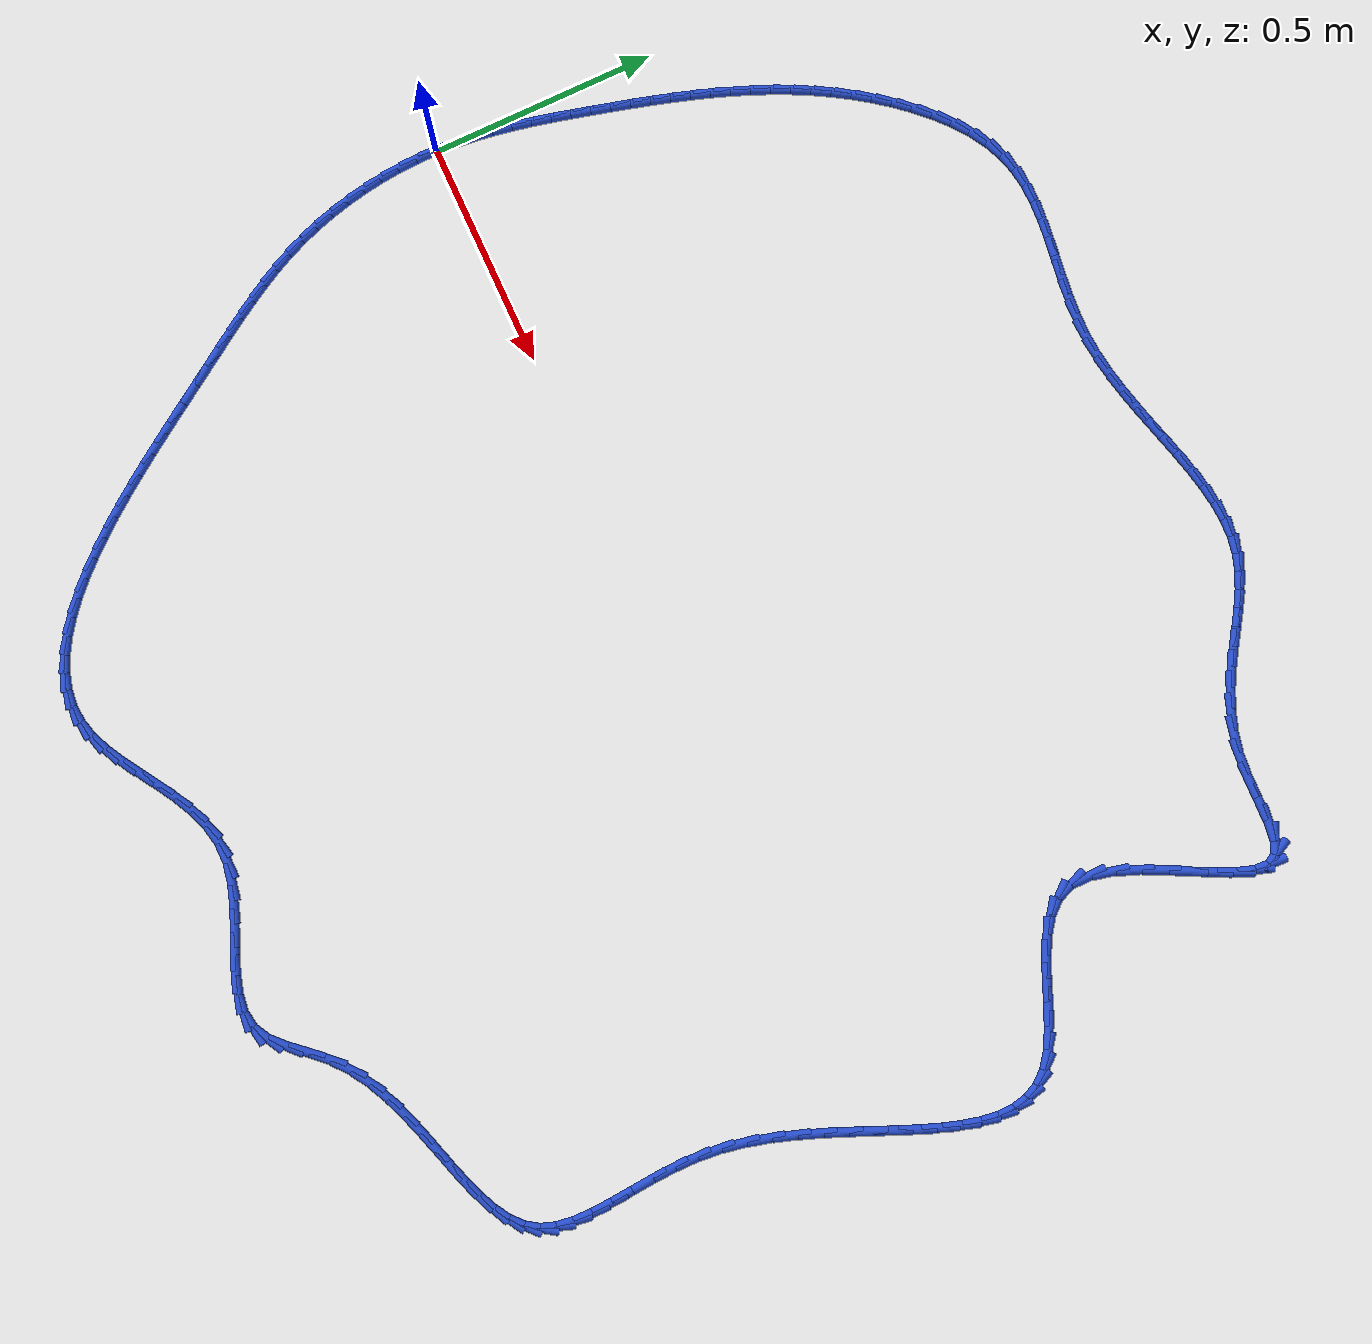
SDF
<sdf version="1.6">
 <world name="default">
  <light name="sun" type="directional">
   <pose>0 0 10 0 -0 0</pose>
   <diffuse>0.8 0.8 0.8 1</diffuse>
   <specular>0.2 0.2 0.2 1</specular>
   <attenuation>
    <range>1000</range>
    <constant>0.9</constant>
    <linear>0.01</linear>
    <quadratic>0.001</quadratic>
   </attenuation>
   <direction>-0.5 0.1 -0.9</direction>
  </light>
  <model name="ground_plane">
   <static>1</static>
   <link name="link">
    <collision name="collision">
     <geometry><plane><normal>0 0 1</normal><size>100 100</size></plane></geometry>
     <surface><friction><ode><mu>100</mu><mu2>50</mu2></ode></friction></surface>
    </collision>
    <visual name="visual">
     <cast_shadows>0</cast_shadows>
     <geometry><plane><normal>0 0 1</normal><size>100 100</size></plane></geometry>
     <material>
      <script><uri>file://media/materials/scripts/gazebo.material</uri><name>Gazebo/WhiteGlow</name></script>
     </material>
    </visual>
   </link>
  </model>
  <gravity>0 0 -9.8</gravity>
  <magnetic_field>6e-06 2.3e-05 -4.2e-05</magnetic_field>
  <atmosphere type="adiabatic"/>
  <physics name="default_physics" default="0" type="ode">
   <max_step_size>0.001</max_step_size>
   <real_time_factor>1</real_time_factor>
   <real_time_update_rate>1000</real_time_update_rate>
  </physics>
  <scene><ambient>0.4 0.4 0.4 1</ambient><background>0.7 0.7 0.7 1</background><shadows>1</shadows></scene>
  <spherical_coordinates>
   <surface_model>EARTH_WGS84</surface_model>
   <latitude_deg>0</latitude_deg>
   <longitude_deg>0</longitude_deg>
   <elevation>0</elevation>
   <heading_deg>0</heading_deg>
  </spherical_coordinates>
  <model name="line">
   <link name="link_0">
    <pose>-3.469446951953614e-18 2.7755575615628914e-17 0.01 0 1.57 1.5192770141631684</pose>
    <collision name="collision">
     <geometry><cylinder><radius>0.01</radius><length>0.08</length></cylinder></geometry>
    </collision>
    <visual name="visual">
     <material>
      <script><name>Gazebo/Blue</name><uri>file://media/materials/scripts/gazebo.material</uri></script>
     </material>
     <geometry><cylinder><radius>0.01</radius><length>0.08</length></cylinder></geometry>
    </visual>
   </link>
   <link name="link_1">
    <pose>0.0022234696732677346 0.04311979342382623 0.01 0 1.57 1.4721471994053563</pose>
    <collision name="collision">
     <geometry><cylinder><radius>0.01</radius><length>0.08</length></cylinder></geometry>
    </collision>
    <visual name="visual">
     <material>
      <script><name>Gazebo/Blue</name><uri>file://media/materials/scripts/gazebo.material</uri></script>
     </material>
     <geometry><cylinder><radius>0.01</radius><length>0.08</length></cylinder></geometry>
    </visual>
   </link>
   <link name="link_2">
    <pose>0.0064593573812255015 0.08591934138477471 0.01 0 1.57 1.4309773788883353</pose>
    <collision name="collision">
     <geometry><cylinder><radius>0.01</radius><length>0.08</length></cylinder></geometry>
    </collision>
    <visual name="visual">
     <material>
      <script><name>Gazebo/Blue</name><uri>file://media/materials/scripts/gazebo.material</uri></script>
     </material>
     <geometry><cylinder><radius>0.01</radius><length>0.08</length></cylinder></geometry>
    </visual>
   </link>
   <link name="link_3">
    <pose>0.012443802629762442 0.12844145375418758 0.01 0 1.57 1.3959717470039945</pose>
    <collision name="collision">
     <geometry><cylinder><radius>0.01</radius><length>0.08</length></cylinder></geometry>
    </collision>
    <visual name="visual">
     <material>
      <script><name>Gazebo/Blue</name><uri>file://media/materials/scripts/gazebo.material</uri></script>
     </material>
     <geometry><cylinder><radius>0.01</radius><length>0.08</length></cylinder></geometry>
    </visual>
   </link>
   <link name="link_4">
    <pose>0.019912944924767716 0.17072894040340683 0.01 0 1.57 1.3672219263026766</pose>
    <collision name="collision">
     <geometry><cylinder><radius>0.01</radius><length>0.08</length></cylinder></geometry>
    </collision>
    <visual name="visual">
     <material>
      <script><name>Gazebo/Blue</name><uri>file://media/materials/scripts/gazebo.material</uri></script>
     </material>
     <geometry><cylinder><radius>0.01</radius><length>0.08</length></cylinder></geometry>
    </visual>
   </link>
   <link name="link_5">
    <pose>0.028602923772130452 0.21282461120377447 0.01 0 1.57 1.3447455544574447</pose>
    <collision name="collision">
     <geometry><cylinder><radius>0.01</radius><length>0.08</length></cylinder></geometry>
    </collision>
    <visual name="visual">
     <material>
      <script><name>Gazebo/Blue</name><uri>file://media/materials/scripts/gazebo.material</uri></script>
     </material>
     <geometry><cylinder><radius>0.01</radius><length>0.08</length></cylinder></geometry>
    </visual>
   </link>
   <link name="link_6">
    <pose>0.03824987867773981 0.2547712760266326 0.01 0 1.57 1.3285198606982707</pose>
    <collision name="collision">
     <geometry><cylinder><radius>0.01</radius><length>0.08</length></cylinder></geometry>
    </collision>
    <visual name="visual">
     <material>
      <script><name>Gazebo/Blue</name><uri>file://media/materials/scripts/gazebo.material</uri></script>
     </material>
     <geometry><cylinder><radius>0.01</radius><length>0.08</length></cylinder></geometry>
    </visual>
   </link>
   <link name="link_7">
    <pose>0.04858994914748492 0.2966117447433232 0.01 0 1.57 1.3185081648030037</pose>
    <collision name="collision">
     <geometry><cylinder><radius>0.01</radius><length>0.08</length></cylinder></geometry>
    </collision>
    <visual name="visual">
     <material>
      <script><name>Gazebo/Blue</name><uri>file://media/materials/scripts/gazebo.material</uri></script>
     </material>
     <geometry><cylinder><radius>0.01</radius><length>0.08</length></cylinder></geometry>
    </visual>
   </link>
   <link name="link_8">
    <pose>0.05935927468725496 0.3383888272251882 0.01 0 1.57 1.3134630752312044</pose>
    <collision name="collision">
     <geometry><cylinder><radius>0.01</radius><length>0.08</length></cylinder></geometry>
    </collision>
    <visual name="visual">
     <material>
      <script><name>Gazebo/Blue</name><uri>file://media/materials/scripts/gazebo.material</uri></script>
     </material>
     <geometry><cylinder><radius>0.01</radius><length>0.08</length></cylinder></geometry>
    </visual>
   </link>
   <link name="link_9">
    <pose>0.07034483380812126 0.38013233437455646 0.01 0 1.57 1.3070497024468977</pose>
    <collision name="collision">
     <geometry><cylinder><radius>0.01</radius><length>0.08</length></cylinder></geometry>
    </collision>
    <visual name="visual">
     <material>
      <script><name>Gazebo/Blue</name><uri>file://media/materials/scripts/gazebo.material</uri></script>
     </material>
     <geometry><cylinder><radius>0.01</radius><length>0.08</length></cylinder></geometry>
    </visual>
   </link>
   <link name="link_10">
    <pose>0.08159787562917808 0.42180450603424297 0.01 0 1.57 1.2972108795401542</pose>
    <collision name="collision">
     <geometry><cylinder><radius>0.01</radius><length>0.08</length></cylinder></geometry>
    </collision>
    <visual name="visual">
     <material>
      <script><name>Gazebo/Blue</name><uri>file://media/materials/scripts/gazebo.material</uri></script>
     </material>
     <geometry><cylinder><radius>0.01</radius><length>0.08</length></cylinder></geometry>
    </visual>
   </link>
   <link name="link_11">
    <pose>0.09325524970200837 0.4633456949671423 0.01 0 1.57 1.283928789996485</pose>
    <collision name="collision">
     <geometry><cylinder><radius>0.01</radius><length>0.08</length></cylinder></geometry>
    </collision>
    <visual name="visual">
     <material>
      <script><name>Gazebo/Blue</name><uri>file://media/materials/scripts/gazebo.material</uri></script>
     </material>
     <geometry><cylinder><radius>0.01</radius><length>0.08</length></cylinder></geometry>
    </visual>
   </link>
   <link name="link_12">
    <pose>0.10545384949938895 0.5046962427059888 0.01 0 1.57 1.2671825491414752</pose>
    <collision name="collision">
     <geometry><cylinder><radius>0.01</radius><length>0.08</length></cylinder></geometry>
    </collision>
    <visual name="visual">
     <material>
      <script><name>Gazebo/Blue</name><uri>file://media/materials/scripts/gazebo.material</uri></script>
     </material>
     <geometry><cylinder><radius>0.01</radius><length>0.08</length></cylinder></geometry>
    </visual>
   </link>
   <link name="link_13">
    <pose>0.11833056849409648 0.5457964907835161 0.01 0 1.57 1.2469518492633453</pose>
    <collision name="collision">
     <geometry><cylinder><radius>0.01</radius><length>0.08</length></cylinder></geometry>
    </collision>
    <visual name="visual">
     <material>
      <script><name>Gazebo/Blue</name><uri>file://media/materials/scripts/gazebo.material</uri></script>
     </material>
     <geometry><cylinder><radius>0.01</radius><length>0.08</length></cylinder></geometry>
    </visual>
   </link>
   <link name="link_14">
    <pose>0.13202230015890765 0.5865867807324583 0.01 0 1.57 1.2232230078182669</pose>
    <collision name="collision">
     <geometry><cylinder><radius>0.01</radius><length>0.08</length></cylinder></geometry>
    </collision>
    <visual name="visual">
     <material>
      <script><name>Gazebo/Blue</name><uri>file://media/materials/scripts/gazebo.material</uri></script>
     </material>
     <geometry><cylinder><radius>0.01</radius><length>0.08</length></cylinder></geometry>
    </visual>
   </link>
   <link name="link_15">
    <pose>0.14666593796659913 0.6270074540855488 0.01 0 1.57 1.1959963902612292</pose>
    <collision name="collision">
     <geometry><cylinder><radius>0.01</radius><length>0.08</length></cylinder></geometry>
    </collision>
    <visual name="visual">
     <material>
      <script><name>Gazebo/Blue</name><uri>file://media/materials/scripts/gazebo.material</uri></script>
     </material>
     <geometry><cylinder><radius>0.01</radius><length>0.08</length></cylinder></geometry>
    </visual>
   </link>
   <link name="link_16">
    <pose>0.16239837538994767 0.6669988523755218 0.01 0 1.57 1.1652951197070973</pose>
    <collision name="collision">
     <geometry><cylinder><radius>0.01</radius><length>0.08</length></cylinder></geometry>
    </collision>
    <visual name="visual">
     <material>
      <script><name>Gazebo/Blue</name><uri>file://media/materials/scripts/gazebo.material</uri></script>
     </material>
     <geometry><cylinder><radius>0.01</radius><length>0.08</length></cylinder></geometry>
    </visual>
   </link>
   <link name="link_17">
    <pose>0.17935650590172997 0.706501317135111 0.01 0 1.57 1.1311748071902608</pose>
    <collision name="collision">
     <geometry><cylinder><radius>0.01</radius><length>0.08</length></cylinder></geometry>
    </collision>
    <visual name="visual">
     <material>
      <script><name>Gazebo/Blue</name><uri>file://media/materials/scripts/gazebo.material</uri></script>
     </material>
     <geometry><cylinder><radius>0.01</radius><length>0.08</length></cylinder></geometry>
    </visual>
   </link>
   <link name="link_18">
    <pose>0.19767722297472273 0.7454551898970503 0.01 0 1.57 1.093733787667848</pose>
    <collision name="collision">
     <geometry><cylinder><radius>0.01</radius><length>0.08</length></cylinder></geometry>
    </collision>
    <visual name="visual">
     <material>
      <script><name>Gazebo/Blue</name><uri>file://media/materials/scripts/gazebo.material</uri></script>
     </material>
     <geometry><cylinder><radius>0.01</radius><length>0.08</length></cylinder></geometry>
    </visual>
   </link>
   <link name="link_19">
    <pose>0.21749742008170259 0.7838008121940734 0.01 0 1.57 1.0531230459847631</pose>
    <collision name="collision">
     <geometry><cylinder><radius>0.01</radius><length>0.08</length></cylinder></geometry>
    </collision>
    <visual name="visual">
     <material>
      <script><name>Gazebo/Blue</name><uri>file://media/materials/scripts/gazebo.material</uri></script>
     </material>
     <geometry><cylinder><radius>0.01</radius><length>0.08</length></cylinder></geometry>
    </visual>
   </link>
   <link name="link_20">
    <pose>0.23895399069544634 0.8214785255589144 0.01 0 1.57 1.0095547104252511</pose>
    <collision name="collision">
     <geometry><cylinder><radius>0.01</radius><length>0.08</length></cylinder></geometry>
    </collision>
    <visual name="visual">
     <material>
      <script><name>Gazebo/Blue</name><uri>file://media/materials/scripts/gazebo.material</uri></script>
     </material>
     <geometry><cylinder><radius>0.01</radius><length>0.08</length></cylinder></geometry>
    </visual>
   </link>
   <link name="link_21">
    <pose>0.26218382828873055 0.8584286715243068 0.01 0 1.57 0.9633077590041591</pose>
    <collision name="collision">
     <geometry><cylinder><radius>0.01</radius><length>0.08</length></cylinder></geometry>
    </collision>
    <visual name="visual">
     <material>
      <script><name>Gazebo/Blue</name><uri>file://media/materials/scripts/gazebo.material</uri></script>
     </material>
     <geometry><cylinder><radius>0.01</radius><length>0.08</length></cylinder></geometry>
    </visual>
   </link>
   <link name="link_22">
    <pose>0.2873238263343321 0.8945915916229848 0.01 0 1.57 0.9147232409143099</pose>
    <collision name="collision">
     <geometry><cylinder><radius>0.01</radius><length>0.08</length></cylinder></geometry>
    </collision>
    <visual name="visual">
     <material>
      <script><name>Gazebo/Blue</name><uri>file://media/materials/scripts/gazebo.material</uri></script>
     </material>
     <geometry><cylinder><radius>0.01</radius><length>0.08</length></cylinder></geometry>
    </visual>
   </link>
   <link name="link_23">
    <pose>0.31451054101376075 0.9299067297663363 0.01 0 1.57 0.8625304937888792</pose>
    <collision name="collision">
     <geometry><cylinder><radius>0.01</radius><length>0.08</length></cylinder></geometry>
    </collision>
    <visual name="visual">
     <material>
      <script><name>Gazebo/Blue</name><uri>file://media/materials/scripts/gazebo.material</uri></script>
     </material>
     <geometry><cylinder><radius>0.01</radius><length>0.08</length></cylinder></geometry>
    </visual>
   </link>
   <link name="link_24">
    <pose>0.3438023296840615 0.964105422093742 0.01 0 1.57 0.8021036056812297</pose>
    <collision name="collision">
     <geometry><cylinder><radius>0.01</radius><length>0.08</length></cylinder></geometry>
    </collision>
    <visual name="visual">
     <material>
      <script><name>Gazebo/Blue</name><uri>file://media/materials/scripts/gazebo.material</uri></script>
     </material>
     <geometry><cylinder><radius>0.01</radius><length>0.08</length></cylinder></geometry>
    </visual>
   </link>
   <link name="link_25">
    <pose>0.3750796703886356 0.9964456208043246 0.01 0 1.57 0.7305967726556333</pose>
    <collision name="collision">
     <geometry><cylinder><radius>0.01</radius><length>0.08</length></cylinder></geometry>
    </collision>
    <visual name="visual">
     <material>
      <script><name>Gazebo/Blue</name><uri>file://media/materials/scripts/gazebo.material</uri></script>
     </material>
     <geometry><cylinder><radius>0.01</radius><length>0.08</length></cylinder></geometry>
    </visual>
   </link>
   <link name="link_26">
    <pose>0.4081984358355471 1.0261197967865683 0.01 0 1.57 0.6451273715583974</pose>
    <collision name="collision">
     <geometry><cylinder><radius>0.01</radius><length>0.08</length></cylinder></geometry>
    </collision>
    <visual name="visual">
     <material>
      <script><name>Gazebo/Blue</name><uri>file://media/materials/scripts/gazebo.material</uri></script>
     </material>
     <geometry><cylinder><radius>0.01</radius><length>0.08</length></cylinder></geometry>
    </visual>
   </link>
   <link name="link_27">
    <pose>0.4430144987328608 1.0523204209289578 0.01 0 1.57 0.5423985255488557</pose>
    <collision name="collision">
     <geometry><cylinder><radius>0.01</radius><length>0.08</length></cylinder></geometry>
    </collision>
    <visual name="visual">
     <material>
      <script><name>Gazebo/Blue</name><uri>file://media/materials/scripts/gazebo.material</uri></script>
     </material>
     <geometry><cylinder><radius>0.01</radius><length>0.08</length></cylinder></geometry>
    </visual>
   </link>
   <link name="link_28">
    <pose>0.47938373178864135 1.0742399641199776 0.01 0 1.57 0.41912113552550395</pose>
    <collision name="collision">
     <geometry><cylinder><radius>0.01</radius><length>0.08</length></cylinder></geometry>
    </collision>
    <visual name="visual">
     <material>
      <script><name>Gazebo/Blue</name><uri>file://media/materials/scripts/gazebo.material</uri></script>
     </material>
     <geometry><cylinder><radius>0.01</radius><length>0.08</length></cylinder></geometry>
    </visual>
   </link>
   <link name="link_29">
    <pose>0.5171620077109534 1.0910708972481116 0.01 0 1.57 0.27546425779916234</pose>
    <collision name="collision">
     <geometry><cylinder><radius>0.01</radius><length>0.08</length></cylinder></geometry>
    </collision>
    <visual name="visual">
     <material>
      <script><name>Gazebo/Blue</name><uri>file://media/materials/scripts/gazebo.material</uri></script>
     </material>
     <geometry><cylinder><radius>0.01</radius><length>0.08</length></cylinder></geometry>
    </visual>
   </link>
   <link name="link_30">
    <pose>0.5562066526863165 1.1021068621475054 0.01 0 1.57 0.13876813090118184</pose>
    <collision name="collision">
     <geometry><cylinder><radius>0.01</radius><length>0.08</length></cylinder></geometry>
    </collision>
    <visual name="visual">
     <material>
      <script><name>Gazebo/Blue</name><uri>file://media/materials/scripts/gazebo.material</uri></script>
     </material>
     <geometry><cylinder><radius>0.01</radius><length>0.08</length></cylinder></geometry>
    </visual>
   </link>
   <link name="link_31">
    <pose>0.5963904752602469 1.1077191670569437 0.01 0 1.57 0.029384992090393188</pose>
    <collision name="collision">
     <geometry><cylinder><radius>0.01</radius><length>0.08</length></cylinder></geometry>
    </collision>
    <visual name="visual">
     <material>
      <script><name>Gazebo/Blue</name><uri>file://media/materials/scripts/gazebo.material</uri></script>
     </material>
     <geometry><cylinder><radius>0.01</radius><length>0.08</length></cylinder></geometry>
    </visual>
   </link>
   <link name="link_32">
    <pose>0.637595639609872 1.108930329109342 0.01 0 1.57 -0.05121354719147642</pose>
    <collision name="collision">
     <geometry><cylinder><radius>0.01</radius><length>0.08</length></cylinder></geometry>
    </collision>
    <visual name="visual">
     <material>
      <script><name>Gazebo/Blue</name><uri>file://media/materials/scripts/gazebo.material</uri></script>
     </material>
     <geometry><cylinder><radius>0.01</radius><length>0.08</length></cylinder></geometry>
    </visual>
   </link>
   <link name="link_33">
    <pose>0.6797044397179012 1.1067719006960488 0.01 0 1.57 -0.10444417231424875</pose>
    <collision name="collision">
     <geometry><cylinder><radius>0.01</radius><length>0.08</length></cylinder></geometry>
    </collision>
    <visual name="visual">
     <material>
      <script><name>Gazebo/Blue</name><uri>file://media/materials/scripts/gazebo.material</uri></script>
     </material>
     <geometry><cylinder><radius>0.01</radius><length>0.08</length></cylinder></geometry>
    </visual>
   </link>
   <link name="link_34">
    <pose>0.7225991695670426 1.102275434208411 0.01 0 1.57 -0.13242879782485945</pose>
    <collision name="collision">
     <geometry><cylinder><radius>0.01</radius><length>0.08</length></cylinder></geometry>
    </collision>
    <visual name="visual">
     <material>
      <script><name>Gazebo/Blue</name><uri>file://media/materials/scripts/gazebo.material</uri></script>
     </material>
     <geometry><cylinder><radius>0.01</radius><length>0.08</length></cylinder></geometry>
    </visual>
   </link>
   <link name="link_35">
    <pose>0.7661621231400063 1.0964724820377765 0.01 0 1.57 -0.13691643023261096</pose>
    <collision name="collision">
     <geometry><cylinder><radius>0.01</radius><length>0.08</length></cylinder></geometry>
    </collision>
    <visual name="visual">
     <material>
      <script><name>Gazebo/Blue</name><uri>file://media/materials/scripts/gazebo.material</uri></script>
     </material>
     <geometry><cylinder><radius>0.01</radius><length>0.08</length></cylinder></geometry>
    </visual>
   </link>
   <link name="link_36">
    <pose>0.8102755944195007 1.0903945965754933 0.01 0 1.57 -0.1188914095847734</pose>
    <collision name="collision">
     <geometry><cylinder><radius>0.01</radius><length>0.08</length></cylinder></geometry>
    </collision>
    <visual name="visual">
     <material>
      <script><name>Gazebo/Blue</name><uri>file://media/materials/scripts/gazebo.material</uri></script>
     </material>
     <geometry><cylinder><radius>0.01</radius><length>0.08</length></cylinder></geometry>
    </visual>
   </link>
   <link name="link_37">
    <pose>0.8548218773882349 1.0850733302129083 0.01 0 1.57 -0.0785935833890232</pose>
    <collision name="collision">
     <geometry><cylinder><radius>0.01</radius><length>0.08</length></cylinder></geometry>
    </collision>
    <visual name="visual">
     <material>
      <script><name>Gazebo/Blue</name><uri>file://media/materials/scripts/gazebo.material</uri></script>
     </material>
     <geometry><cylinder><radius>0.01</radius><length>0.08</length></cylinder></geometry>
    </visual>
   </link>
   <link name="link_38">
    <pose>0.8996832660289179 1.0815402353413701 0.01 0 1.57 -0.01583068303377196</pose>
    <collision name="collision">
     <geometry><cylinder><radius>0.01</radius><length>0.08</length></cylinder></geometry>
    </collision>
    <visual name="visual">
     <material>
      <script><name>Gazebo/Blue</name><uri>file://media/materials/scripts/gazebo.material</uri></script>
     </material>
     <geometry><cylinder><radius>0.01</radius><length>0.08</length></cylinder></geometry>
    </visual>
   </link>
   <link name="link_39">
    <pose>0.9447420543242586 1.0808268643522256 0.01 0 1.57 0.06521968606140681</pose>
    <collision name="collision">
     <geometry><cylinder><radius>0.01</radius><length>0.08</length></cylinder></geometry>
    </collision>
    <visual name="visual">
     <material>
      <script><name>Gazebo/Blue</name><uri>file://media/materials/scripts/gazebo.material</uri></script>
     </material>
     <geometry><cylinder><radius>0.01</radius><length>0.08</length></cylinder></geometry>
    </visual>
   </link>
   <link name="link_40">
    <pose>0.9898814048950397 1.0837750199101297 0.01 0 1.57 0.13864147830354148</pose>
    <collision name="collision">
     <geometry><cylinder><radius>0.01</radius><length>0.08</length></cylinder></geometry>
    </collision>
    <visual name="visual">
     <material>
      <script><name>Gazebo/Blue</name><uri>file://media/materials/scripts/gazebo.material</uri></script>
     </material>
     <geometry><cylinder><radius>0.01</radius><length>0.08</length></cylinder></geometry>
    </visual>
   </link>
   <link name="link_41">
    <pose>1.0349897778630974 1.0900692915576036 0.01 0 1.57 0.19515393980822712</pose>
    <collision name="collision">
     <geometry><cylinder><radius>0.01</radius><length>0.08</length></cylinder></geometry>
    </collision>
    <visual name="visual">
     <material>
      <script><name>Gazebo/Blue</name><uri>file://media/materials/scripts/gazebo.material</uri></script>
     </material>
     <geometry><cylinder><radius>0.01</radius><length>0.08</length></cylinder></geometry>
    </visual>
   </link>
   <link name="link_42">
    <pose>1.0799576301581613 1.0989580759467232 0.01 0 1.57 0.23551589524179659</pose>
    <collision name="collision">
     <geometry><cylinder><radius>0.01</radius><length>0.08</length></cylinder></geometry>
    </collision>
    <visual name="visual">
     <material>
      <script><name>Gazebo/Blue</name><uri>file://media/materials/scripts/gazebo.material</uri></script>
     </material>
     <geometry><cylinder><radius>0.01</radius><length>0.08</length></cylinder></geometry>
    </visual>
   </link>
   <link name="link_43">
    <pose>1.1246754223685365 1.1096889705316333 0.01 0 1.57 0.26042876316129226</pose>
    <collision name="collision">
     <geometry><cylinder><radius>0.01</radius><length>0.08</length></cylinder></geometry>
    </collision>
    <visual name="visual">
     <material>
      <script><name>Gazebo/Blue</name><uri>file://media/materials/scripts/gazebo.material</uri></script>
     </material>
     <geometry><cylinder><radius>0.01</radius><length>0.08</length></cylinder></geometry>
    </visual>
   </link>
   <link name="link_44">
    <pose>1.1690336150825291 1.1215095727664806 0.01 0 1.57 0.2702381736349711</pose>
    <collision name="collision">
     <geometry><cylinder><radius>0.01</radius><length>0.08</length></cylinder></geometry>
    </collision>
    <visual name="visual">
     <material>
      <script><name>Gazebo/Blue</name><uri>file://media/materials/scripts/gazebo.material</uri></script>
     </material>
     <geometry><cylinder><radius>0.01</radius><length>0.08</length></cylinder></geometry>
    </visual>
   </link>
   <link name="link_45">
    <pose>1.212922668888443 1.1336674801054099 0.01 0 1.57 0.26476621296448294</pose>
    <collision name="collision">
     <geometry><cylinder><radius>0.01</radius><length>0.08</length></cylinder></geometry>
    </collision>
    <visual name="visual">
     <material>
      <script><name>Gazebo/Blue</name><uri>file://media/materials/scripts/gazebo.material</uri></script>
     </material>
     <geometry><cylinder><radius>0.01</radius><length>0.08</length></cylinder></geometry>
    </visual>
   </link>
   <link name="link_46">
    <pose>1.2562330443745857 1.145410290002569 0.01 0 1.57 0.243206262841886</pose>
    <collision name="collision">
     <geometry><cylinder><radius>0.01</radius><length>0.08</length></cylinder></geometry>
    </collision>
    <visual name="visual">
     <material>
      <script><name>Gazebo/Blue</name><uri>file://media/materials/scripts/gazebo.material</uri></script>
     </material>
     <geometry><cylinder><radius>0.01</radius><length>0.08</length></cylinder></geometry>
    </visual>
   </link>
   <link name="link_47">
    <pose>1.2988552021292605 1.1559855999121016 0.01 0 1.57 0.20406574075876835</pose>
    <collision name="collision">
     <geometry><cylinder><radius>0.01</radius><length>0.08</length></cylinder></geometry>
    </collision>
    <visual name="visual">
     <material>
      <script><name>Gazebo/Blue</name><uri>file://media/materials/scripts/gazebo.material</uri></script>
     </material>
     <geometry><cylinder><radius>0.01</radius><length>0.08</length></cylinder></geometry>
    </visual>
   </link>
   <link name="link_48">
    <pose>1.340679602740774 1.1646410072881557 0.01 0 1.57 0.14519595741874367</pose>
    <collision name="collision">
     <geometry><cylinder><radius>0.01</radius><length>0.08</length></cylinder></geometry>
    </collision>
    <visual name="visual">
     <material>
      <script><name>Gazebo/Blue</name><uri>file://media/materials/scripts/gazebo.material</uri></script>
     </material>
     <geometry><cylinder><radius>0.01</radius><length>0.08</length></cylinder></geometry>
    </visual>
   </link>
   <link name="link_49">
    <pose>1.3815967067974313 1.1706241095848755 0.01 0 1.57 0.06403207982112052</pose>
    <collision name="collision">
     <geometry><cylinder><radius>0.01</radius><length>0.08</length></cylinder></geometry>
    </collision>
    <visual name="visual">
     <material>
      <script><name>Gazebo/Blue</name><uri>file://media/materials/scripts/gazebo.material</uri></script>
     </material>
     <geometry><cylinder><radius>0.01</radius><length>0.08</length></cylinder></geometry>
    </visual>
   </link>
   <link name="link_50">
    <pose>1.4214969748875377 1.1731825042564084 0.01 0 1.57 -0.04172333420575803</pose>
    <collision name="collision">
     <geometry><cylinder><radius>0.01</radius><length>0.08</length></cylinder></geometry>
    </collision>
    <visual name="visual">
     <material>
      <script><name>Gazebo/Blue</name><uri>file://media/materials/scripts/gazebo.material</uri></script>
     </material>
     <geometry><cylinder><radius>0.01</radius><length>0.08</length></cylinder></geometry>
    </visual>
   </link>
   <link name="link_51">
    <pose>1.460270867599398 1.1715637887568984 0.01 0 1.57 -0.172704927068935</pose>
    <collision name="collision">
     <geometry><cylinder><radius>0.01</radius><length>0.08</length></cylinder></geometry>
    </collision>
    <visual name="visual">
     <material>
      <script><name>Gazebo/Blue</name><uri>file://media/materials/scripts/gazebo.material</uri></script>
     </material>
     <geometry><cylinder><radius>0.01</radius><length>0.08</length></cylinder></geometry>
    </visual>
   </link>
   <link name="link_52">
    <pose>1.4978088455213197 1.165015560540493 0.01 0 1.57 -0.3195023220120659</pose>
    <collision name="collision">
     <geometry><cylinder><radius>0.01</radius><length>0.08</length></cylinder></geometry>
    </collision>
    <visual name="visual">
     <material>
      <script><name>Gazebo/Blue</name><uri>file://media/materials/scripts/gazebo.material</uri></script>
     </material>
     <geometry><cylinder><radius>0.01</radius><length>0.08</length></cylinder></geometry>
    </visual>
   </link>
   <link name="link_53">
    <pose>1.5340769796274079 1.1530167139164735 0.01 0 1.57 -0.44034441701610094</pose>
    <collision name="collision">
     <geometry><cylinder><radius>0.01</radius><length>0.08</length></cylinder></geometry>
    </collision>
    <visual name="visual">
     <material>
      <script><name>Gazebo/Blue</name><uri>file://media/materials/scripts/gazebo.material</uri></script>
     </material>
     <geometry><cylinder><radius>0.01</radius><length>0.08</length></cylinder></geometry>
    </visual>
   </link>
   <link name="link_54">
    <pose>1.5694649117307469 1.136341872635817 0.01 0 1.57 -0.5212878407982343</pose>
    <collision name="collision">
     <geometry><cylinder><radius>0.01</radius><length>0.08</length></cylinder></geometry>
    </collision>
    <visual name="visual">
     <material>
      <script><name>Gazebo/Blue</name><uri>file://media/materials/scripts/gazebo.material</uri></script>
     </material>
     <geometry><cylinder><radius>0.01</radius><length>0.08</length></cylinder></geometry>
    </visual>
   </link>
   <link name="link_55">
    <pose>1.604509693510012 1.1162165963621486 0.01 0 1.57 -0.565212544174314</pose>
    <collision name="collision">
     <geometry><cylinder><radius>0.01</radius><length>0.08</length></cylinder></geometry>
    </collision>
    <visual name="visual">
     <material>
      <script><name>Gazebo/Blue</name><uri>file://media/materials/scripts/gazebo.material</uri></script>
     </material>
     <geometry><cylinder><radius>0.01</radius><length>0.08</length></cylinder></geometry>
    </visual>
   </link>
   <link name="link_56">
    <pose>1.6397485259787012 1.093866901583568 0.01 0 1.57 -0.5757406119897641</pose>
    <collision name="collision">
     <geometry><cylinder><radius>0.01</radius><length>0.08</length></cylinder></geometry>
    </collision>
    <visual name="visual">
     <material>
      <script><name>Gazebo/Blue</name><uri>file://media/materials/scripts/gazebo.material</uri></script>
     </material>
     <geometry><cylinder><radius>0.01</radius><length>0.08</length></cylinder></geometry>
    </visual>
   </link>
   <link name="link_57">
    <pose>1.6757186101503105 1.0705188047881729 0.01 0 1.57 -0.5556276335707667</pose>
    <collision name="collision">
     <geometry><cylinder><radius>0.01</radius><length>0.08</length></cylinder></geometry>
    </collision>
    <visual name="visual">
     <material>
      <script><name>Gazebo/Blue</name><uri>file://media/materials/scripts/gazebo.material</uri></script>
     </material>
     <geometry><cylinder><radius>0.01</radius><length>0.08</length></cylinder></geometry>
    </visual>
   </link>
   <link name="link_58">
    <pose>1.7129571470383385 1.0473983224640606 0.01 0 1.57 -0.5066215073512923</pose>
    <collision name="collision">
     <geometry><cylinder><radius>0.01</radius><length>0.08</length></cylinder></geometry>
    </collision>
    <visual name="visual">
     <material>
      <script><name>Gazebo/Blue</name><uri>file://media/materials/scripts/gazebo.material</uri></script>
     </material>
     <geometry><cylinder><radius>0.01</radius><length>0.08</length></cylinder></geometry>
    </visual>
   </link>
   <link name="link_59">
    <pose>1.7520013376562806 1.0257314710993297 0.01 0 1.57 -0.4301244598763836</pose>
    <collision name="collision">
     <geometry><cylinder><radius>0.01</radius><length>0.08</length></cylinder></geometry>
    </collision>
    <visual name="visual">
     <material>
      <script><name>Gazebo/Blue</name><uri>file://media/materials/scripts/gazebo.material</uri></script>
     </material>
     <geometry><cylinder><radius>0.01</radius><length>0.08</length></cylinder></geometry>
    </visual>
   </link>
   <link name="link_60">
    <pose>1.7933883830176351 1.0067442671820779 0.01 0 1.57 -0.3283605476052916</pose>
    <collision name="collision">
     <geometry><cylinder><radius>0.01</radius><length>0.08</length></cylinder></geometry>
    </collision>
    <visual name="visual">
     <material>
      <script><name>Gazebo/Blue</name><uri>file://media/materials/scripts/gazebo.material</uri></script>
     </material>
     <geometry><cylinder><radius>0.01</radius><length>0.08</length></cylinder></geometry>
    </visual>
   </link>
   <link name="link_61">
    <pose>1.8376554841358985 0.9916627272004038 0.01 0 1.57 -0.20570927977166567</pose>
    <collision name="collision">
     <geometry><cylinder><radius>0.01</radius><length>0.08</length></cylinder></geometry>
    </collision>
    <visual name="visual">
     <material>
      <script><name>Gazebo/Blue</name><uri>file://media/materials/scripts/gazebo.material</uri></script>
     </material>
     <geometry><cylinder><radius>0.01</radius><length>0.08</length></cylinder></geometry>
    </visual>
   </link>
   <link name="link_62">
    <pose>1.885339842024568 0.981712867642405 0.01 0 1.57 -0.08412807927843689</pose>
    <collision name="collision">
     <geometry><cylinder><radius>0.01</radius><length>0.08</length></cylinder></geometry>
    </collision>
    <visual name="visual">
     <material>
      <script><name>Gazebo/Blue</name><uri>file://media/materials/scripts/gazebo.material</uri></script>
     </material>
     <geometry><cylinder><radius>0.01</radius><length>0.08</length></cylinder></geometry>
    </visual>
   </link>
   <link name="link_63">
    <pose>1.9362745459773723 0.9774176909599253 0.01 0 1.57 -0.0230302165221149</pose>
    <collision name="collision">
     <geometry><cylinder><radius>0.01</radius><length>0.08</length></cylinder></geometry>
    </collision>
    <visual name="visual">
     <material>
      <script><name>Gazebo/Blue</name><uri>file://media/materials/scripts/gazebo.material</uri></script>
     </material>
     <geometry><cylinder><radius>0.01</radius><length>0.08</length></cylinder></geometry>
    </visual>
   </link>
   <link name="link_64">
    <pose>1.9872316440687687 0.9762439304329135 0.01 0 1.57 -0.030168695830535077</pose>
    <collision name="collision">
     <geometry><cylinder><radius>0.01</radius><length>0.08</length></cylinder></geometry>
    </collision>
    <visual name="visual">
     <material>
      <script><name>Gazebo/Blue</name><uri>file://media/materials/scripts/gazebo.material</uri></script>
     </material>
     <geometry><cylinder><radius>0.01</radius><length>0.08</length></cylinder></geometry>
    </visual>
   </link>
   <link name="link_65">
    <pose>2.034151556813516 0.9748279882574994 0.01 0 1.57 -0.1286348896563046</pose>
    <collision name="collision">
     <geometry><cylinder><radius>0.01</radius><length>0.08</length></cylinder></geometry>
    </collision>
    <visual name="visual">
     <material>
      <script><name>Gazebo/Blue</name><uri>file://media/materials/scripts/gazebo.material</uri></script>
     </material>
     <geometry><cylinder><radius>0.01</radius><length>0.08</length></cylinder></geometry>
    </visual>
   </link>
   <link name="link_66">
    <pose>2.0729746883595292 0.9698062502884848 0.01 0 1.57 -0.4225766071582267</pose>
    <collision name="collision">
     <geometry><cylinder><radius>0.01</radius><length>0.08</length></cylinder></geometry>
    </collision>
    <visual name="visual">
     <material>
      <script><name>Gazebo/Blue</name><uri>file://media/materials/scripts/gazebo.material</uri></script>
     </material>
     <geometry><cylinder><radius>0.01</radius><length>0.08</length></cylinder></geometry>
    </visual>
   </link>
   <link name="link_67">
    <pose>2.099641442854722 0.9578151023806711 0.01 0 1.57 -1.079901413770883</pose>
    <collision name="collision">
     <geometry><cylinder><radius>0.01</radius><length>0.08</length></cylinder></geometry>
    </collision>
    <visual name="visual">
     <material>
      <script><name>Gazebo/Blue</name><uri>file://media/materials/scripts/gazebo.material</uri></script>
     </material>
     <geometry><cylinder><radius>0.01</radius><length>0.08</length></cylinder></geometry>
    </visual>
   </link>
   <link name="link_68">
    <pose>2.1111670909713003 0.936253223719382 0.01 0 1.57 1.509301783870213</pose>
    <collision name="collision">
     <geometry><cylinder><radius>0.01</radius><length>0.08</length></cylinder></geometry>
    </collision>
    <visual name="visual">
     <material>
      <script><name>Gazebo/Blue</name><uri>file://media/materials/scripts/gazebo.material</uri></script>
     </material>
     <geometry><cylinder><radius>0.01</radius><length>0.08</length></cylinder></geometry>
    </visual>
   </link>
   <link name="link_69">
    <pose>2.1092965482862343 0.9058735488185439 0.01 0 1.57 1.2559235450657842</pose>
    <collision name="collision">
     <geometry><cylinder><radius>0.01</radius><length>0.08</length></cylinder></geometry>
    </collision>
    <visual name="visual">
     <material>
      <script><name>Gazebo/Blue</name><uri>file://media/materials/scripts/gazebo.material</uri></script>
     </material>
     <geometry><cylinder><radius>0.01</radius><length>0.08</length></cylinder></geometry>
    </visual>
   </link>
   <link name="link_70">
    <pose>2.097075233075772 0.8683513262762789 0.01 0 1.57 1.1444396874630016</pose>
    <collision name="collision">
     <geometry><cylinder><radius>0.01</radius><length>0.08</length></cylinder></geometry>
    </collision>
    <visual name="visual">
     <material>
      <script><name>Gazebo/Blue</name><uri>file://media/materials/scripts/gazebo.material</uri></script>
     </material>
     <geometry><cylinder><radius>0.01</radius><length>0.08</length></cylinder></geometry>
    </visual>
   </link>
   <link name="link_71">
    <pose>2.0775486015807476 0.825361831615125 0.01 0 1.57 1.1004040789737013</pose>
    <collision name="collision">
     <geometry><cylinder><radius>0.01</radius><length>0.08</length></cylinder></geometry>
    </collision>
    <visual name="visual">
     <material>
      <script><name>Gazebo/Blue</name><uri>file://media/materials/scripts/gazebo.material</uri></script>
     </material>
     <geometry><cylinder><radius>0.01</radius><length>0.08</length></cylinder></geometry>
    </visual>
   </link>
   <link name="link_72">
    <pose>2.053762110042004 0.7785803403576236 0.01 0 1.57 1.0981619692004918</pose>
    <collision name="collision">
     <geometry><cylinder><radius>0.01</radius><length>0.08</length></cylinder></geometry>
    </collision>
    <visual name="visual">
     <material>
      <script><name>Gazebo/Blue</name><uri>file://media/materials/scripts/gazebo.material</uri></script>
     </material>
     <geometry><cylinder><radius>0.01</radius><length>0.08</length></cylinder></geometry>
    </visual>
   </link>
   <link name="link_73">
    <pose>2.028761214700378 0.7296821280263144 0.01 0 1.57 1.1317641207325282</pose>
    <collision name="collision">
     <geometry><cylinder><radius>0.01</radius><length>0.08</length></cylinder></geometry>
    </collision>
    <visual name="visual">
     <material>
      <script><name>Gazebo/Blue</name><uri>file://media/materials/scripts/gazebo.material</uri></script>
     </material>
     <geometry><cylinder><radius>0.01</radius><length>0.08</length></cylinder></geometry>
    </visual>
   </link>
   <link name="link_74">
    <pose>2.0055913717967098 0.6803424701437361 0.01 0 1.57 1.2074110265667841</pose>
    <collision name="collision">
     <geometry><cylinder><radius>0.01</radius><length>0.08</length></cylinder></geometry>
    </collision>
    <visual name="visual">
     <material>
      <script><name>Gazebo/Blue</name><uri>file://media/materials/scripts/gazebo.material</uri></script>
     </material>
     <geometry><cylinder><radius>0.01</radius><length>0.08</length></cylinder></geometry>
    </visual>
   </link>
   <link name="link_75">
    <pose>1.9872980375718368 0.6322366422324299 0.01 0 1.57 1.345229741580537</pose>
    <collision name="collision">
     <geometry><cylinder><radius>0.01</radius><length>0.08</length></cylinder></geometry>
    </collision>
    <visual name="visual">
     <material>
      <script><name>Gazebo/Blue</name><uri>file://media/materials/scripts/gazebo.material</uri></script>
     </material>
     <geometry><cylinder><radius>0.01</radius><length>0.08</length></cylinder></geometry>
    </visual>
   </link>
   <link name="link_76">
    <pose>1.976926668266599 0.5870399198149353 0.01 0 1.57 -1.5561207616081631</pose>
    <collision name="collision">
     <geometry><cylinder><radius>0.01</radius><length>0.08</length></cylinder></geometry>
    </collision>
    <visual name="visual">
     <material>
      <script><name>Gazebo/Blue</name><uri>file://media/materials/scripts/gazebo.material</uri></script>
     </material>
     <geometry><cylinder><radius>0.01</radius><length>0.08</length></cylinder></geometry>
    </visual>
   </link>
   <link name="link_77">
    <pose>1.9775227201218342 0.5464275784137915 0.01 0 1.57 -1.1911691524824919</pose>
    <collision name="collision">
     <geometry><cylinder><radius>0.01</radius><length>0.08</length></cylinder></geometry>
    </collision>
    <visual name="visual">
     <material>
      <script><name>Gazebo/Blue</name><uri>file://media/materials/scripts/gazebo.material</uri></script>
     </material>
     <geometry><cylinder><radius>0.01</radius><length>0.08</length></cylinder></geometry>
    </visual>
   </link>
   <link name="link_78">
    <pose>1.991375269947519 0.511707710112623 0.01 0 1.57 -0.8541834276953869</pose>
    <collision name="collision">
     <geometry><cylinder><radius>0.01</radius><length>0.08</length></cylinder></geometry>
    </collision>
    <visual name="visual">
     <material>
      <script><name>Gazebo/Blue</name><uri>file://media/materials/scripts/gazebo.material</uri></script>
     </material>
     <geometry><cylinder><radius>0.01</radius><length>0.08</length></cylinder></geometry>
    </visual>
   </link>
   <link name="link_79">
    <pose>2.0169598006536513 0.4823371026553433 0.01 0 1.57 -0.6285751039968146</pose>
    <collision name="collision">
     <geometry><cylinder><radius>0.01</radius><length>0.08</length></cylinder></geometry>
    </collision>
    <visual name="visual">
     <material>
      <script><name>Gazebo/Blue</name><uri>file://media/materials/scripts/gazebo.material</uri></script>
     </material>
     <geometry><cylinder><radius>0.01</radius><length>0.08</length></cylinder></geometry>
    </visual>
   </link>
   <link name="link_80">
    <pose>2.051552602912916 0.45719039742961715 0.01 0 1.57 -0.49465646691797727</pose>
    <collision name="collision">
     <geometry><cylinder><radius>0.01</radius><length>0.08</length></cylinder></geometry>
    </collision>
    <visual name="visual">
     <material>
      <script><name>Gazebo/Blue</name><uri>file://media/materials/scripts/gazebo.material</uri></script>
     </material>
     <geometry><cylinder><radius>0.01</radius><length>0.08</length></cylinder></geometry>
    </visual>
   </link>
   <link name="link_81">
    <pose>2.0924295300891473 0.43514202353208215 0.01 0 1.57 -0.424331475846428</pose>
    <collision name="collision">
     <geometry><cylinder><radius>0.01</radius><length>0.08</length></cylinder></geometry>
    </collision>
    <visual name="visual">
     <material>
      <script><name>Gazebo/Blue</name><uri>file://media/materials/scripts/gazebo.material</uri></script>
     </material>
     <geometry><cylinder><radius>0.01</radius><length>0.08</length></cylinder></geometry>
    </visual>
   </link>
   <link name="link_82">
    <pose>2.1368664355461826 0.4150664100593753 0.01 0 1.57 -0.4016369612314232</pose>
    <collision name="collision">
     <geometry><cylinder><radius>0.01</radius><length>0.08</length></cylinder></geometry>
    </collision>
    <visual name="visual">
     <material>
      <script><name>Gazebo/Blue</name><uri>file://media/materials/scripts/gazebo.material</uri></script>
     </material>
     <geometry><cylinder><radius>0.01</radius><length>0.08</length></cylinder></geometry>
    </visual>
   </link>
   <link name="link_83">
    <pose>2.182139172647858 0.3958379861081334 0.01 0 1.57 -0.42254365303032254</pose>
    <collision name="collision">
     <geometry><cylinder><radius>0.01</radius><length>0.08</length></cylinder></geometry>
    </collision>
    <visual name="visual">
     <material>
      <script><name>Gazebo/Blue</name><uri>file://media/materials/scripts/gazebo.material</uri></script>
     </material>
     <geometry><cylinder><radius>0.01</radius><length>0.08</length></cylinder></geometry>
    </visual>
   </link>
   <link name="link_84">
    <pose>2.2255235947580085 0.3763311807749943 0.01 0 1.57 -0.49461190760615836</pose>
    <collision name="collision">
     <geometry><cylinder><radius>0.01</radius><length>0.08</length></cylinder></geometry>
    </collision>
    <visual name="visual">
     <material>
      <script><name>Gazebo/Blue</name><uri>file://media/materials/scripts/gazebo.material</uri></script>
     </material>
     <geometry><cylinder><radius>0.01</radius><length>0.08</length></cylinder></geometry>
    </visual>
   </link>
   <link name="link_85">
    <pose>2.264295555240471 0.35542042315659456 0.01 0 1.57 -0.6404566331524179</pose>
    <collision name="collision">
     <geometry><cylinder><radius>0.01</radius><length>0.08</length></cylinder></geometry>
    </collision>
    <visual name="visual">
     <material>
      <script><name>Gazebo/Blue</name><uri>file://media/materials/scripts/gazebo.material</uri></script>
     </material>
     <geometry><cylinder><radius>0.01</radius><length>0.08</length></cylinder></geometry>
    </visual>
   </link>
   <link name="link_86">
    <pose>2.2957425171723185 0.3319844543555239 0.01 0 1.57 -0.8676320434695225</pose>
    <collision name="collision">
     <geometry><cylinder><radius>0.01</radius><length>0.08</length></cylinder></geometry>
    </collision>
    <visual name="visual">
     <material>
      <script><name>Gazebo/Blue</name><uri>file://media/materials/scripts/gazebo.material</uri></script>
     </material>
     <geometry><cylinder><radius>0.01</radius><length>0.08</length></cylinder></geometry>
    </visual>
   </link>
   <link name="link_87">
    <pose>2.3183297820394775 0.30533948073521877 0.01 0 1.57 -1.120626432364721</pose>
    <collision name="collision">
     <geometry><cylinder><radius>0.01</radius><length>0.08</length></cylinder></geometry>
    </collision>
    <visual name="visual">
     <material>
      <script><name>Gazebo/Blue</name><uri>file://media/materials/scripts/gazebo.material</uri></script>
     </material>
     <geometry><cylinder><radius>0.01</radius><length>0.08</length></cylinder></geometry>
    </visual>
   </link>
   <link name="link_88">
    <pose>2.3326972803740347 0.2756093955674159 0.01 0 1.57 -1.3586519014329288</pose>
    <collision name="collision">
     <geometry><cylinder><radius>0.01</radius><length>0.08</length></cylinder></geometry>
    </collision>
    <visual name="visual">
     <material>
      <script><name>Gazebo/Blue</name><uri>file://media/materials/scripts/gazebo.material</uri></script>
     </material>
     <geometry><cylinder><radius>0.01</radius><length>0.08</length></cylinder></geometry>
    </visual>
   </link>
   <link name="link_89">
    <pose>2.3397197252800863 0.2430052935755408 0.01 0 1.57 -1.555142624802687</pose>
    <collision name="collision">
     <geometry><cylinder><radius>0.01</radius><length>0.08</length></cylinder></geometry>
    </collision>
    <visual name="visual">
     <material>
      <script><name>Gazebo/Blue</name><uri>file://media/materials/scripts/gazebo.material</uri></script>
     </material>
     <geometry><cylinder><radius>0.01</radius><length>0.08</length></cylinder></geometry>
    </visual>
   </link>
   <link name="link_90">
    <pose>2.3402718298617247 0.2077382694830172 0.01 0 1.57 1.4378712089685903</pose>
    <collision name="collision">
     <geometry><cylinder><radius>0.01</radius><length>0.08</length></cylinder></geometry>
    </collision>
    <visual name="visual">
     <material>
      <script><name>Gazebo/Blue</name><uri>file://media/materials/scripts/gazebo.material</uri></script>
     </material>
     <geometry><cylinder><radius>0.01</radius><length>0.08</length></cylinder></geometry>
    </visual>
   </link>
   <link name="link_91">
    <pose>2.335228307223044 0.17001941801327003 0.01 0 1.57 1.3311349623608568</pose>
    <collision name="collision">
     <geometry><cylinder><radius>0.01</radius><length>0.08</length></cylinder></geometry>
    </collision>
    <visual name="visual">
     <material>
      <script><name>Gazebo/Blue</name><uri>file://media/materials/scripts/gazebo.material</uri></script>
     </material>
     <geometry><cylinder><radius>0.01</radius><length>0.08</length></cylinder></geometry>
    </visual>
   </link>
   <link name="link_92">
    <pose>2.325463870468139 0.13005983388972275 0.01 0 1.57 1.2573370483364759</pose>
    <collision name="collision">
     <geometry><cylinder><radius>0.01</radius><length>0.08</length></cylinder></geometry>
    </collision>
    <visual name="visual">
     <material>
      <script><name>Gazebo/Blue</name><uri>file://media/materials/scripts/gazebo.material</uri></script>
     </material>
     <geometry><cylinder><radius>0.01</radius><length>0.08</length></cylinder></geometry>
    </visual>
   </link>
   <link name="link_93">
    <pose>2.311853232701103 0.0880706118358016 0.01 0 1.57 1.2089429990774962</pose>
    <collision name="collision">
     <geometry><cylinder><radius>0.01</radius><length>0.08</length></cylinder></geometry>
    </collision>
    <visual name="visual">
     <material>
      <script><name>Gazebo/Blue</name><uri>file://media/materials/scripts/gazebo.material</uri></script>
     </material>
     <geometry><cylinder><radius>0.01</radius><length>0.08</length></cylinder></geometry>
    </visual>
   </link>
   <link name="link_94">
    <pose>2.2952711070260308 0.04426284657493024 0.01 0 1.57 1.1805937842309817</pose>
    <collision name="collision">
     <geometry><cylinder><radius>0.01</radius><length>0.08</length></cylinder></geometry>
    </collision>
    <visual name="visual">
     <material>
      <script><name>Gazebo/Blue</name><uri>file://media/materials/scripts/gazebo.material</uri></script>
     </material>
     <geometry><cylinder><radius>0.01</radius><length>0.08</length></cylinder></geometry>
    </visual>
   </link>
   <link name="link_95">
    <pose>2.2765922065470154 -0.0011523671694668308 0.01 0 1.57 1.1688162882435027</pose>
    <collision name="collision">
     <geometry><cylinder><radius>0.01</radius><length>0.08</length></cylinder></geometry>
    </collision>
    <visual name="visual">
     <material>
      <script><name>Gazebo/Blue</name><uri>file://media/materials/scripts/gazebo.material</uri></script>
     </material>
     <geometry><cylinder><radius>0.01</radius><length>0.08</length></cylinder></geometry>
    </visual>
   </link>
   <link name="link_96">
    <pose>2.256691244368152 -0.047963934673964995 0.01 0 1.57 1.1715817550994596</pose>
    <collision name="collision">
     <geometry><cylinder><radius>0.01</radius><length>0.08</length></cylinder></geometry>
    </collision>
    <visual name="visual">
     <material>
      <script><name>Gazebo/Blue</name><uri>file://media/materials/scripts/gazebo.material</uri></script>
     </material>
     <geometry><cylinder><radius>0.01</radius><length>0.08</length></cylinder></geometry>
    </visual>
   </link>
   <link name="link_97">
    <pose>2.236442933593533 -0.0959607612151398 0.01 0 1.57 1.1879587651145824</pose>
    <collision name="collision">
     <geometry><cylinder><radius>0.01</radius><length>0.08</length></cylinder></geometry>
    </collision>
    <visual name="visual">
     <material>
      <script><name>Gazebo/Blue</name><uri>file://media/materials/scripts/gazebo.material</uri></script>
     </material>
     <geometry><cylinder><radius>0.01</radius><length>0.08</length></cylinder></geometry>
    </visual>
   </link>
   <link name="link_98">
    <pose>2.2167219873272535 -0.1449317520695677 0.01 0 1.57 1.2178804080635466</pose>
    <collision name="collision">
     <geometry><cylinder><radius>0.01</radius><length>0.08</length></cylinder></geometry>
    </collision>
    <visual name="visual">
     <material>
      <script><name>Gazebo/Blue</name><uri>file://media/materials/scripts/gazebo.material</uri></script>
     </material>
     <geometry><cylinder><radius>0.01</radius><length>0.08</length></cylinder></geometry>
    </visual>
   </link>
   <link name="link_99">
    <pose>2.1984031186734074 -0.1946658125138222 0.01 0 1.57 1.261985727884241</pose>
    <collision name="collision">
     <geometry><cylinder><radius>0.01</radius><length>0.08</length></cylinder></geometry>
    </collision>
    <visual name="visual">
     <material>
      <script><name>Gazebo/Blue</name><uri>file://media/materials/scripts/gazebo.material</uri></script>
     </material>
     <geometry><cylinder><radius>0.01</radius><length>0.08</length></cylinder></geometry>
    </visual>
   </link>
   <link name="link_100">
    <pose>2.1823610407360885 -0.24495184782447965 0.01 0 1.57 1.321475125162975</pose>
    <collision name="collision">
     <geometry><cylinder><radius>0.01</radius><length>0.08</length></cylinder></geometry>
    </collision>
    <visual name="visual">
     <material>
      <script><name>Gazebo/Blue</name><uri>file://media/materials/scripts/gazebo.material</uri></script>
     </material>
     <geometry><cylinder><radius>0.01</radius><length>0.08</length></cylinder></geometry>
    </visual>
   </link>
   <link name="link_101">
    <pose>2.169470466619391 -0.29557876327811583 0.01 0 1.57 1.397896027643031</pose>
    <collision name="collision">
     <geometry><cylinder><radius>0.01</radius><length>0.08</length></cylinder></geometry>
    </collision>
    <visual name="visual">
     <material>
      <script><name>Gazebo/Blue</name><uri>file://media/materials/scripts/gazebo.material</uri></script>
     </material>
     <geometry><cylinder><radius>0.01</radius><length>0.08</length></cylinder></geometry>
    </visual>
   </link>
   <link name="link_102">
    <pose>2.160606109427409 -0.3463354641513059 0.01 0 1.57 1.4894826770412086</pose>
    <collision name="collision">
     <geometry><cylinder><radius>0.01</radius><length>0.08</length></cylinder></geometry>
    </collision>
    <visual name="visual">
     <material>
      <script><name>Gazebo/Blue</name><uri>file://media/materials/scripts/gazebo.material</uri></script>
     </material>
     <geometry><cylinder><radius>0.01</radius><length>0.08</length></cylinder></geometry>
    </visual>
   </link>
   <link name="link_103">
    <pose>2.1564782502383184 -0.39698818373186995 0.01 0 1.57 1.569157032402854</pose>
    <collision name="collision">
     <geometry><cylinder><radius>0.01</radius><length>0.08</length></cylinder></geometry>
    </collision>
    <visual name="visual">
     <material>
      <script><name>Gazebo/Blue</name><uri>file://media/materials/scripts/gazebo.material</uri></script>
     </material>
     <geometry><cylinder><radius>0.01</radius><length>0.08</length></cylinder></geometry>
    </visual>
   </link>
   <link name="link_104">
    <pose>2.1563960857967523 -0.44710997293892396 0.01 0 1.57 -1.5185904190248332</pose>
    <collision name="collision">
     <geometry><cylinder><radius>0.01</radius><length>0.08</length></cylinder></geometry>
    </collision>
    <visual name="visual">
     <material>
      <script><name>Gazebo/Blue</name><uri>file://media/materials/scripts/gazebo.material</uri></script>
     </material>
     <geometry><cylinder><radius>0.01</radius><length>0.08</length></cylinder></geometry>
    </visual>
   </link>
   <link name="link_105">
    <pose>2.1589599595450952 -0.49617614556277095 0.01 0 1.57 -1.490841781544966</pose>
    <collision name="collision">
     <geometry><cylinder><radius>0.01</radius><length>0.08</length></cylinder></geometry>
    </collision>
    <visual name="visual">
     <material>
      <script><name>Gazebo/Blue</name><uri>file://media/materials/scripts/gazebo.material</uri></script>
     </material>
     <geometry><cylinder><radius>0.01</radius><length>0.08</length></cylinder></geometry>
    </visual>
   </link>
   <link name="link_106">
    <pose>2.1627647211701997 -0.5436612579113247 0.01 0 1.57 -1.4907427686726116</pose>
    <collision name="collision">
     <geometry><cylinder><radius>0.01</radius><length>0.08</length></cylinder></geometry>
    </collision>
    <visual name="visual">
     <material>
      <script><name>Gazebo/Blue</name><uri>file://media/materials/scripts/gazebo.material</uri></script>
     </material>
     <geometry><cylinder><radius>0.01</radius><length>0.08</length></cylinder></geometry>
    </visual>
   </link>
   <link name="link_107">
    <pose>2.1664052203589184 -0.5890398662924993 0.01 0 1.57 -1.5223839336788507</pose>
    <collision name="collision">
     <geometry><cylinder><radius>0.01</radius><length>0.08</length></cylinder></geometry>
    </collision>
    <visual name="visual">
     <material>
      <script><name>Gazebo/Blue</name><uri>file://media/materials/scripts/gazebo.material</uri></script>
     </material>
     <geometry><cylinder><radius>0.01</radius><length>0.08</length></cylinder></geometry>
    </visual>
   </link>
   <link name="link_108">
    <pose>2.168476306798104 -0.6317865270142089 0.01 0 1.57 1.547979037148773</pose>
    <collision name="collision">
     <geometry><cylinder><radius>0.01</radius><length>0.08</length></cylinder></geometry>
    </collision>
    <visual name="visual">
     <material>
      <script><name>Gazebo/Blue</name><uri>file://media/materials/scripts/gazebo.material</uri></script>
     </material>
     <geometry><cylinder><radius>0.01</radius><length>0.08</length></cylinder></geometry>
    </visual>
   </link>
   <link name="link_109">
    <pose>2.167572830174609 -0.6713757963843678 0.01 0 1.57 1.4247068676211814</pose>
    <collision name="collision">
     <geometry><cylinder><radius>0.01</radius><length>0.08</length></cylinder></geometry>
    </collision>
    <visual name="visual">
     <material>
      <script><name>Gazebo/Blue</name><uri>file://media/materials/scripts/gazebo.material</uri></script>
     </material>
     <geometry><cylinder><radius>0.01</radius><length>0.08</length></cylinder></geometry>
    </visual>
   </link>
   <link name="link_110">
    <pose>2.1622896401752865 -0.7072822307108889 0.01 0 1.57 1.2348608749621917</pose>
    <collision name="collision">
     <geometry><cylinder><radius>0.01</radius><length>0.08</length></cylinder></geometry>
    </collision>
    <visual name="visual">
     <material>
      <script><name>Gazebo/Blue</name><uri>file://media/materials/scripts/gazebo.material</uri></script>
     </material>
     <geometry><cylinder><radius>0.01</radius><length>0.08</length></cylinder></geometry>
    </visual>
   </link>
   <link name="link_111">
    <pose>2.15122158648699 -0.7389803863016867 0.01 0 1.57 0.980181670290711</pose>
    <collision name="collision">
     <geometry><cylinder><radius>0.01</radius><length>0.08</length></cylinder></geometry>
    </collision>
    <visual name="visual">
     <material>
      <script><name>Gazebo/Blue</name><uri>file://media/materials/scripts/gazebo.material</uri></script>
     </material>
     <geometry><cylinder><radius>0.01</radius><length>0.08</length></cylinder></geometry>
    </visual>
   </link>
   <link name="link_112">
    <pose>2.133093909534444 -0.7660186130096834 0.01 0 1.57 0.7364895926720736</pose>
    <collision name="collision">
     <geometry><cylinder><radius>0.01</radius><length>0.08</length></cylinder></geometry>
    </collision>
    <visual name="visual">
     <material>
      <script><name>Gazebo/Blue</name><uri>file://media/materials/scripts/gazebo.material</uri></script>
     </material>
     <geometry><cylinder><radius>0.01</radius><length>0.08</length></cylinder></geometry>
    </visual>
   </link>
   <link name="link_113">
    <pose>2.1080346509819634 -0.7887391642893884 0.01 0 1.57 0.5550685959691314</pose>
    <collision name="collision">
     <geometry><cylinder><radius>0.01</radius><length>0.08</length></cylinder></geometry>
    </collision>
    <visual name="visual">
     <material>
      <script><name>Gazebo/Blue</name><uri>file://media/materials/scripts/gazebo.material</uri></script>
     </material>
     <geometry><cylinder><radius>0.01</radius><length>0.08</length></cylinder></geometry>
    </visual>
   </link>
   <link name="link_114">
    <pose>2.077025970452677 -0.8079676744938645 0.01 0 1.57 0.4317260269761285</pose>
    <collision name="collision">
     <geometry><cylinder><radius>0.01</radius><length>0.08</length></cylinder></geometry>
    </collision>
    <visual name="visual">
     <material>
      <script><name>Gazebo/Blue</name><uri>file://media/materials/scripts/gazebo.material</uri></script>
     </material>
     <geometry><cylinder><radius>0.01</radius><length>0.08</length></cylinder></geometry>
    </visual>
   </link>
   <link name="link_115">
    <pose>2.0410621407753435 -0.8245366333433539 0.01 0 1.57 0.3537134465056357</pose>
    <collision name="collision">
     <geometry><cylinder><radius>0.01</radius><length>0.08</length></cylinder></geometry>
    </collision>
    <visual name="visual">
     <material>
      <script><name>Gazebo/Blue</name><uri>file://media/materials/scripts/gazebo.material</uri></script>
     </material>
     <geometry><cylinder><radius>0.01</radius><length>0.08</length></cylinder></geometry>
    </visual>
   </link>
   <link name="link_116">
    <pose>2.001137434778725 -0.8392785305580979 0.01 0 1.57 0.31017040173664784</pose>
    <collision name="collision">
     <geometry><cylinder><radius>0.01</radius><length>0.08</length></cylinder></geometry>
    </collision>
    <visual name="visual">
     <material>
      <script><name>Gazebo/Blue</name><uri>file://media/materials/scripts/gazebo.material</uri></script>
     </material>
     <geometry><cylinder><radius>0.01</radius><length>0.08</length></cylinder></geometry>
    </visual>
   </link>
   <link name="link_117">
    <pose>1.9582461252915795 -0.8530258558583387 0.01 0 1.57 0.2940344979994388</pose>
    <collision name="collision">
     <geometry><cylinder><radius>0.01</radius><length>0.08</length></cylinder></geometry>
    </collision>
    <visual name="visual">
     <material>
      <script><name>Gazebo/Blue</name><uri>file://media/materials/scripts/gazebo.material</uri></script>
     </material>
     <geometry><cylinder><radius>0.01</radius><length>0.08</length></cylinder></geometry>
    </visual>
   </link>
   <link name="link_118">
    <pose>1.9133824851426688 -0.866611098964319 0.01 0 1.57 0.30149551088402143</pose>
    <collision name="collision">
     <geometry><cylinder><radius>0.01</radius><length>0.08</length></cylinder></geometry>
    </collision>
    <visual name="visual">
     <material>
      <script><name>Gazebo/Blue</name><uri>file://media/materials/scripts/gazebo.material</uri></script>
     </material>
     <geometry><cylinder><radius>0.01</radius><length>0.08</length></cylinder></geometry>
    </visual>
   </link>
   <link name="link_119">
    <pose>1.8675407871607514 -0.8808667495962801 0.01 0 1.57 0.33121391060313654</pose>
    <collision name="collision">
     <geometry><cylinder><radius>0.01</radius><length>0.08</length></cylinder></geometry>
    </collision>
    <visual name="visual">
     <material>
      <script><name>Gazebo/Blue</name><uri>file://media/materials/scripts/gazebo.material</uri></script>
     </material>
     <geometry><cylinder><radius>0.01</radius><length>0.08</length></cylinder></geometry>
    </visual>
   </link>
   <link name="link_120">
    <pose>1.8217153041745873 -0.8966252974744651 0.01 0 1.57 0.38373265777856513</pose>
    <collision name="collision">
     <geometry><cylinder><radius>0.01</radius><length>0.08</length></cylinder></geometry>
    </collision>
    <visual name="visual">
     <material>
      <script><name>Gazebo/Blue</name><uri>file://media/materials/scripts/gazebo.material</uri></script>
     </material>
     <geometry><cylinder><radius>0.01</radius><length>0.08</length></cylinder></geometry>
    </visual>
   </link>
   <link name="link_121">
    <pose>1.7769003090129387 -0.914719232319115 0.01 0 1.57 0.4609660535810747</pose>
    <collision name="collision">
     <geometry><cylinder><radius>0.01</radius><length>0.08</length></cylinder></geometry>
    </collision>
    <visual name="visual">
     <material>
      <script><name>Gazebo/Blue</name><uri>file://media/materials/scripts/gazebo.material</uri></script>
     </material>
     <geometry><cylinder><radius>0.01</radius><length>0.08</length></cylinder></geometry>
    </visual>
   </link>
   <link name="link_122">
    <pose>1.7340900745045635 -0.9359810438504725 0.01 0 1.57 0.5654369222945441</pose>
    <collision name="collision">
     <geometry><cylinder><radius>0.01</radius><length>0.08</length></cylinder></geometry>
    </collision>
    <visual name="visual">
     <material>
      <script><name>Gazebo/Blue</name><uri>file://media/materials/scripts/gazebo.material</uri></script>
     </material>
     <geometry><cylinder><radius>0.01</radius><length>0.08</length></cylinder></geometry>
    </visual>
   </link>
   <link name="link_123">
    <pose>1.6942788734782224 -0.9612432217887794 0.01 0 1.57 0.6986126161108204</pose>
    <collision name="collision">
     <geometry><cylinder><radius>0.01</radius><length>0.08</length></cylinder></geometry>
    </collision>
    <visual name="visual">
     <material>
      <script><name>Gazebo/Blue</name><uri>file://media/materials/scripts/gazebo.material</uri></script>
     </material>
     <geometry><cylinder><radius>0.01</radius><length>0.08</length></cylinder></geometry>
    </visual>
   </link>
   <link name="link_124">
    <pose>1.6584568610383035 -0.9913308279998385 0.01 0 1.57 0.8209664122551037</pose>
    <collision name="collision">
     <geometry><cylinder><radius>0.01</radius><length>0.08</length></cylinder></geometry>
    </collision>
    <visual name="visual">
     <material>
      <script><name>Gazebo/Blue</name><uri>file://media/materials/scripts/gazebo.material</uri></script>
     </material>
     <geometry><cylinder><radius>0.01</radius><length>0.08</length></cylinder></geometry>
    </visual>
   </link>
   <link name="link_125">
    <pose>1.6267039140278363 -1.0254268973910206 0.01 0 1.57 0.8475652461998507</pose>
    <collision name="collision">
     <geometry><cylinder><radius>0.01</radius><length>0.08</length></cylinder></geometry>
    </collision>
    <visual name="visual">
     <material>
      <script><name>Gazebo/Blue</name><uri>file://media/materials/scripts/gazebo.material</uri></script>
     </material>
     <geometry><cylinder><radius>0.01</radius><length>0.08</length></cylinder></geometry>
    </visual>
   </link>
   <link name="link_126">
    <pose>1.5970503171179289 -1.0590172595832075 0.01 0 1.57 0.7553528224565373</pose>
    <collision name="collision">
     <geometry><cylinder><radius>0.01</radius><length>0.08</length></cylinder></geometry>
    </collision>
    <visual name="visual">
     <material>
      <script><name>Gazebo/Blue</name><uri>file://media/materials/scripts/gazebo.material</uri></script>
     </material>
     <geometry><cylinder><radius>0.01</radius><length>0.08</length></cylinder></geometry>
    </visual>
   </link>
   <link name="link_127">
    <pose>1.5672461194977036 -1.0870822347990339 0.01 0 1.57 0.5000535279477681</pose>
    <collision name="collision">
     <geometry><cylinder><radius>0.01</radius><length>0.08</length></cylinder></geometry>
    </collision>
    <visual name="visual">
     <material>
      <script><name>Gazebo/Blue</name><uri>file://media/materials/scripts/gazebo.material</uri></script>
     </material>
     <geometry><cylinder><radius>0.01</radius><length>0.08</length></cylinder></geometry>
    </visual>
   </link>
   <link name="link_128">
    <pose>1.5350646166413753 -1.1046653067182888 0.01 0 1.57 0.1439521921724851</pose>
    <collision name="collision">
     <geometry><cylinder><radius>0.01</radius><length>0.08</length></cylinder></geometry>
    </collision>
    <visual name="visual">
     <material>
      <script><name>Gazebo/Blue</name><uri>file://media/materials/scripts/gazebo.material</uri></script>
     </material>
     <geometry><cylinder><radius>0.01</radius><length>0.08</length></cylinder></geometry>
    </visual>
   </link>
   <link name="link_129">
    <pose>1.4993928279890663 -1.109836105164405 0.01 0 1.57 -0.1253176762033019</pose>
    <collision name="collision">
     <geometry><cylinder><radius>0.01</radius><length>0.08</length></cylinder></geometry>
    </collision>
    <visual name="visual">
     <material>
      <script><name>Gazebo/Blue</name><uri>file://media/materials/scripts/gazebo.material</uri></script>
     </material>
     <geometry><cylinder><radius>0.01</radius><length>0.08</length></cylinder></geometry>
    </visual>
   </link>
   <link name="link_130">
    <pose>1.4606993326524313 -1.104961582140712 0.01 0 1.57 -0.2889518792990292</pose>
    <collision name="collision">
     <geometry><cylinder><radius>0.01</radius><length>0.08</length></cylinder></geometry>
    </collision>
    <visual name="visual">
     <material>
      <script><name>Gazebo/Blue</name><uri>file://media/materials/scripts/gazebo.material</uri></script>
     </material>
     <geometry><cylinder><radius>0.01</radius><length>0.08</length></cylinder></geometry>
    </visual>
   </link>
   <link name="link_131">
    <pose>1.4195731456670095 -1.092735931155411 0.01 0 1.57 -0.3743652193026448</pose>
    <collision name="collision">
     <geometry><cylinder><radius>0.01</radius><length>0.08</length></cylinder></geometry>
    </collision>
    <visual name="visual">
     <material>
      <script><name>Gazebo/Blue</name><uri>file://media/materials/scripts/gazebo.material</uri></script>
     </material>
     <geometry><cylinder><radius>0.01</radius><length>0.08</length></cylinder></geometry>
    </visual>
   </link>
   <link name="link_132">
    <pose>1.3766032820683414 -1.075853345716705 0.01 0 1.57 -0.4028260284271112</pose>
    <collision name="collision">
     <geometry><cylinder><radius>0.01</radius><length>0.08</length></cylinder></geometry>
    </collision>
    <visual name="visual">
     <material>
      <script><name>Gazebo/Blue</name><uri>file://media/materials/scripts/gazebo.material</uri></script>
     </material>
     <geometry><cylinder><radius>0.01</radius><length>0.08</length></cylinder></geometry>
    </visual>
   </link>
   <link name="link_133">
    <pose>1.3323787568919656 -1.0570080193327962 0.01 0 1.57 -0.3835331819172979</pose>
    <collision name="collision">
     <geometry><cylinder><radius>0.01</radius><length>0.08</length></cylinder></geometry>
    </collision>
    <visual name="visual">
     <material>
      <script><name>Gazebo/Blue</name><uri>file://media/materials/scripts/gazebo.material</uri></script>
     </material>
     <geometry><cylinder><radius>0.01</radius><length>0.08</length></cylinder></geometry>
    </visual>
   </link>
   <link name="link_134">
    <pose>1.2874885851734212 -1.0388941455118863 0.01 0 1.57 -0.3157199557134032</pose>
    <collision name="collision">
     <geometry><cylinder><radius>0.01</radius><length>0.08</length></cylinder></geometry>
    </collision>
    <visual name="visual">
     <material>
      <script><name>Gazebo/Blue</name><uri>file://media/materials/scripts/gazebo.material</uri></script>
     </material>
     <geometry><cylinder><radius>0.01</radius><length>0.08</length></cylinder></geometry>
    </visual>
   </link>
   <link name="link_135">
    <pose>1.2425217819482473 -1.0242059177621772 0.01 0 1.57 -0.19041042200598982</pose>
    <collision name="collision">
     <geometry><cylinder><radius>0.01</radius><length>0.08</length></cylinder></geometry>
    </collision>
    <visual name="visual">
     <material>
      <script><name>Gazebo/Blue</name><uri>file://media/materials/scripts/gazebo.material</uri></script>
     </material>
     <geometry><cylinder><radius>0.01</radius><length>0.08</length></cylinder></geometry>
    </visual>
   </link>
   <link name="link_136">
    <pose>1.1980673622519835 -1.0156375295918714 0.01 0 1.57 0.0015470019989808164</pose>
    <collision name="collision">
     <geometry><cylinder><radius>0.01</radius><length>0.08</length></cylinder></geometry>
    </collision>
    <visual name="visual">
     <material>
      <script><name>Gazebo/Blue</name><uri>file://media/materials/scripts/gazebo.material</uri></script>
     </material>
     <geometry><cylinder><radius>0.01</radius><length>0.08</length></cylinder></geometry>
    </visual>
   </link>
   <link name="link_137">
    <pose>1.1546868965329298 -1.0157046393125915 0.01 0 1.57 0.20348824987113845</pose>
    <collision name="collision">
     <geometry><cylinder><radius>0.01</radius><length>0.08</length></cylinder></geometry>
    </collision>
    <visual name="visual">
     <material>
      <script><name>Gazebo/Blue</name><uri>file://media/materials/scripts/gazebo.material</uri></script>
     </material>
     <geometry><cylinder><radius>0.01</radius><length>0.08</length></cylinder></geometry>
    </visual>
   </link>
   <link name="link_138">
    <pose>1.112553907224546 -1.0243985375707085 0.01 0 1.57 0.3601907374875386</pose>
    <collision name="collision">
     <geometry><cylinder><radius>0.01</radius><length>0.08</length></cylinder></geometry>
    </collision>
    <visual name="visual">
     <material>
      <script><name>Gazebo/Blue</name><uri>file://media/materials/scripts/gazebo.material</uri></script>
     </material>
     <geometry><cylinder><radius>0.01</radius><length>0.08</length></cylinder></geometry>
    </visual>
   </link>
   <link name="link_139">
    <pose>1.0715543512787942 -1.0398398160903686 0.01 0 1.57 0.4690679496773634</pose>
    <collision name="collision">
     <geometry><cylinder><radius>0.01</radius><length>0.08</length></cylinder></geometry>
    </collision>
    <visual name="visual">
     <material>
      <script><name>Gazebo/Blue</name><uri>file://media/materials/scripts/gazebo.material</uri></script>
     </material>
     <geometry><cylinder><radius>0.01</radius><length>0.08</length></cylinder></geometry>
    </visual>
   </link>
   <link name="link_140">
    <pose>1.0315674050395371 -1.0601049567248217 0.01 0 1.57 0.5349168757054185</pose>
    <collision name="collision">
     <geometry><cylinder><radius>0.01</radius><length>0.08</length></cylinder></geometry>
    </collision>
    <visual name="visual">
     <material>
      <script><name>Gazebo/Blue</name><uri>file://media/materials/scripts/gazebo.material</uri></script>
     </material>
     <geometry><cylinder><radius>0.01</radius><length>0.08</length></cylinder></geometry>
    </visual>
   </link>
   <link name="link_141">
    <pose>0.9924722448506373 -1.0832704413273155 0.01 0 1.57 0.5621506137367575</pose>
    <collision name="collision">
     <geometry><cylinder><radius>0.01</radius><length>0.08</length></cylinder></geometry>
    </collision>
    <visual name="visual">
     <material>
      <script><name>Gazebo/Blue</name><uri>file://media/materials/scripts/gazebo.material</uri></script>
     </material>
     <geometry><cylinder><radius>0.01</radius><length>0.08</length></cylinder></geometry>
    </visual>
   </link>
   <link name="link_142">
    <pose>0.9541480470559567 -1.107412751751101 0.01 0 1.57 0.5518779303213867</pose>
    <collision name="collision">
     <geometry><cylinder><radius>0.01</radius><length>0.08</length></cylinder></geometry>
    </collision>
    <visual name="visual">
     <material>
      <script><name>Gazebo/Blue</name><uri>file://media/materials/scripts/gazebo.material</uri></script>
     </material>
     <geometry><cylinder><radius>0.01</radius><length>0.08</length></cylinder></geometry>
    </visual>
   </link>
   <link name="link_143">
    <pose>0.9164739879993602 -1.1306083698494254 0.01 0 1.57 0.5006868909593177</pose>
    <collision name="collision">
     <geometry><cylinder><radius>0.01</radius><length>0.08</length></cylinder></geometry>
    </collision>
    <visual name="visual">
     <material>
      <script><name>Gazebo/Blue</name><uri>file://media/materials/scripts/gazebo.material</uri></script>
     </material>
     <geometry><cylinder><radius>0.01</radius><length>0.08</length></cylinder></geometry>
    </visual>
   </link>
   <link name="link_144">
    <pose>0.879329244024709 -1.1509337774755388 0.01 0 1.57 0.3999963177477569</pose>
    <collision name="collision">
     <geometry><cylinder><radius>0.01</radius><length>0.08</length></cylinder></geometry>
    </collision>
    <visual name="visual">
     <material>
      <script><name>Gazebo/Blue</name><uri>file://media/materials/scripts/gazebo.material</uri></script>
     </material>
     <geometry><cylinder><radius>0.01</radius><length>0.08</length></cylinder></geometry>
    </visual>
   </link>
   <link name="link_145">
    <pose>0.8425929914758664 -1.16646545648269 0.01 0 1.57 0.24186157840503394</pose>
    <collision name="collision">
     <geometry><cylinder><radius>0.01</radius><length>0.08</length></cylinder></geometry>
    </collision>
    <visual name="visual">
     <material>
      <script><name>Gazebo/Blue</name><uri>file://media/materials/scripts/gazebo.material</uri></script>
     </material>
     <geometry><cylinder><radius>0.01</radius><length>0.08</length></cylinder></geometry>
    </visual>
   </link>
   <link name="link_146">
    <pose>0.8061554807344292 -1.1754542502615366 0.01 0 1.57 0.0600854106731669</pose>
    <collision name="collision">
     <geometry><cylinder><radius>0.01</radius><length>0.08</length></cylinder></geometry>
    </collision>
    <visual name="visual">
     <material>
      <script><name>Gazebo/Blue</name><uri>file://media/materials/scripts/gazebo.material</uri></script>
     </material>
     <geometry><cylinder><radius>0.01</radius><length>0.08</length></cylinder></geometry>
    </visual>
   </link>
   <link name="link_147">
    <pose>0.770000847554697 -1.177629234290863 0.01 0 1.57 -0.11569056870551513</pose>
    <collision name="collision">
     <geometry><cylinder><radius>0.01</radius><length>0.08</length></cylinder></geometry>
    </collision>
    <visual name="visual">
     <material>
      <script><name>Gazebo/Blue</name><uri>file://media/materials/scripts/gazebo.material</uri></script>
     </material>
     <geometry><cylinder><radius>0.01</radius><length>0.08</length></cylinder></geometry>
    </visual>
   </link>
   <link name="link_148">
    <pose>0.7341605291538511 -1.1734642490563736 0.01 0 1.57 -0.27528155688643385</pose>
    <collision name="collision">
     <geometry><cylinder><radius>0.01</radius><length>0.08</length></cylinder></geometry>
    </collision>
    <visual name="visual">
     <material>
      <script><name>Gazebo/Blue</name><uri>file://media/materials/scripts/gazebo.material</uri></script>
     </material>
     <geometry><cylinder><radius>0.01</radius><length>0.08</length></cylinder></geometry>
    </visual>
   </link>
   <link name="link_149">
    <pose>0.6986663236884993 -1.1634388180615123 0.01 0 1.57 -0.4134371488589972</pose>
    <collision name="collision">
     <geometry><cylinder><radius>0.01</radius><length>0.08</length></cylinder></geometry>
    </collision>
    <visual name="visual">
     <material>
      <script><name>Gazebo/Blue</name><uri>file://media/materials/scripts/gazebo.material</uri></script>
     </material>
     <geometry><cylinder><radius>0.01</radius><length>0.08</length></cylinder></geometry>
    </visual>
   </link>
   <link name="link_150">
    <pose>0.6635500293152476 -1.1480324648097238 0.01 0 1.57 -0.5294115111573013</pose>
    <collision name="collision">
     <geometry><cylinder><radius>0.01</radius><length>0.08</length></cylinder></geometry>
    </collision>
    <visual name="visual">
     <material>
      <script><name>Gazebo/Blue</name><uri>file://media/materials/scripts/gazebo.material</uri></script>
     </material>
     <geometry><cylinder><radius>0.01</radius><length>0.08</length></cylinder></geometry>
    </visual>
   </link>
   <link name="link_151">
    <pose>0.6288434441907024 -1.1277247128044514 0.01 0 1.57 -0.6251517414823613</pose>
    <collision name="collision">
     <geometry><cylinder><radius>0.01</radius><length>0.08</length></cylinder></geometry>
    </collision>
    <visual name="visual">
     <material>
      <script><name>Gazebo/Blue</name><uri>file://media/materials/scripts/gazebo.material</uri></script>
     </material>
     <geometry><cylinder><radius>0.01</radius><length>0.08</length></cylinder></geometry>
    </visual>
   </link>
   <link name="link_152">
    <pose>0.5945783664714703 -1.1029950855491397 0.01 0 1.57 -0.7036167477557552</pose>
    <collision name="collision">
     <geometry><cylinder><radius>0.01</radius><length>0.08</length></cylinder></geometry>
    </collision>
    <visual name="visual">
     <material>
      <script><name>Gazebo/Blue</name><uri>file://media/materials/scripts/gazebo.material</uri></script>
     </material>
     <geometry><cylinder><radius>0.01</radius><length>0.08</length></cylinder></geometry>
    </visual>
   </link>
   <link name="link_153">
    <pose>0.5607865943141578 -1.0743231065472323 0.01 0 1.57 -0.7677932075517874</pose>
    <collision name="collision">
     <geometry><cylinder><radius>0.01</radius><length>0.08</length></cylinder></geometry>
    </collision>
    <visual name="visual">
     <material>
      <script><name>Gazebo/Blue</name><uri>file://media/materials/scripts/gazebo.material</uri></script>
     </material>
     <geometry><cylinder><radius>0.01</radius><length>0.08</length></cylinder></geometry>
    </visual>
   </link>
   <link name="link_154">
    <pose>0.5274999258753702 -1.042188299302172 0.01 0 1.57 -0.8202804201461357</pose>
    <collision name="collision">
     <geometry><cylinder><radius>0.01</radius><length>0.08</length></cylinder></geometry>
    </collision>
    <visual name="visual">
     <material>
      <script><name>Gazebo/Blue</name><uri>file://media/materials/scripts/gazebo.material</uri></script>
     </material>
     <geometry><cylinder><radius>0.01</radius><length>0.08</length></cylinder></geometry>
    </visual>
   </link>
   <link name="link_155">
    <pose>0.494750159311716 -1.007070187317405 0.01 0 1.57 -0.8631863849559881</pose>
    <collision name="collision">
     <geometry><cylinder><radius>0.01</radius><length>0.08</length></cylinder></geometry>
    </collision>
    <visual name="visual">
     <material>
      <script><name>Gazebo/Blue</name><uri>file://media/materials/scripts/gazebo.material</uri></script>
     </material>
     <geometry><cylinder><radius>0.01</radius><length>0.08</length></cylinder></geometry>
    </visual>
   </link>
   <link name="link_156">
    <pose>0.46256909277980074 -0.9694482940963745 0.01 0 1.57 -0.8981559999890301</pose>
    <collision name="collision">
     <geometry><cylinder><radius>0.01</radius><length>0.08</length></cylinder></geometry>
    </collision>
    <visual name="visual">
     <material>
      <script><name>Gazebo/Blue</name><uri>file://media/materials/scripts/gazebo.material</uri></script>
     </material>
     <geometry><cylinder><radius>0.01</radius><length>0.08</length></cylinder></geometry>
    </visual>
   </link>
   <link name="link_157">
    <pose>0.4309885244362307 -0.9298021431425236 0.01 0 1.57 -0.9264395299572047</pose>
    <collision name="collision">
     <geometry><cylinder><radius>0.01</radius><length>0.08</length></cylinder></geometry>
    </collision>
    <visual name="visual">
     <material>
      <script><name>Gazebo/Blue</name><uri>file://media/materials/scripts/gazebo.material</uri></script>
     </material>
     <geometry><cylinder><radius>0.01</radius><length>0.08</length></cylinder></geometry>
    </visual>
   </link>
   <link name="link_158">
    <pose>0.4000402524376127 -0.8886112579592972 0.01 0 1.57 -0.9489619999095658</pose>
    <collision name="collision">
     <geometry><cylinder><radius>0.01</radius><length>0.08</length></cylinder></geometry>
    </collision>
    <visual name="visual">
     <material>
      <script><name>Gazebo/Blue</name><uri>file://media/materials/scripts/gazebo.material</uri></script>
     </material>
     <geometry><cylinder><radius>0.01</radius><length>0.08</length></cylinder></geometry>
    </visual>
   </link>
   <link name="link_159">
    <pose>0.36975607494055235 -0.8463551620501379 0.01 0 1.57 -0.9663793385086836</pose>
    <collision name="collision">
     <geometry><cylinder><radius>0.01</radius><length>0.08</length></cylinder></geometry>
    </collision>
    <visual name="visual">
     <material>
      <script><name>Gazebo/Blue</name><uri>file://media/materials/scripts/gazebo.material</uri></script>
     </material>
     <geometry><cylinder><radius>0.01</radius><length>0.08</length></cylinder></geometry>
    </visual>
   </link>
   <link name="link_160">
    <pose>0.34016779010165754 -0.8035133789184917 0.01 0 1.57 -0.9791173360593438</pose>
    <collision name="collision">
     <geometry><cylinder><radius>0.01</radius><length>0.08</length></cylinder></geometry>
    </collision>
    <visual name="visual">
     <material>
      <script><name>Gazebo/Blue</name><uri>file://media/materials/scripts/gazebo.material</uri></script>
     </material>
     <geometry><cylinder><radius>0.01</radius><length>0.08</length></cylinder></geometry>
    </visual>
   </link>
   <link name="link_161">
    <pose>0.31130719607753393 -0.7605654320678015 0.01 0 1.57 -0.9873926007474553</pose>
    <collision name="collision">
     <geometry><cylinder><radius>0.01</radius><length>0.08</length></cylinder></geometry>
    </collision>
    <visual name="visual">
     <material>
      <script><name>Gazebo/Blue</name><uri>file://media/materials/scripts/gazebo.material</uri></script>
     </material>
     <geometry><cylinder><radius>0.01</radius><length>0.08</length></cylinder></geometry>
    </visual>
   </link>
   <link name="link_162">
    <pose>0.28320609102478833 -0.7179908450015117 0.01 0 1.57 -0.9912144487094228</pose>
    <collision name="collision">
     <geometry><cylinder><radius>0.01</radius><length>0.08</length></cylinder></geometry>
    </collision>
    <visual name="visual">
     <material>
      <script><name>Gazebo/Blue</name><uri>file://media/materials/scripts/gazebo.material</uri></script>
     </material>
     <geometry><cylinder><radius>0.01</radius><length>0.08</length></cylinder></geometry>
    </visual>
   </link>
   <link name="link_163">
    <pose>0.255896273100027 -0.6762691412230657 0.01 0 1.57 -0.9903744623569157</pose>
    <collision name="collision">
     <geometry><cylinder><radius>0.01</radius><length>0.08</length></cylinder></geometry>
    </collision>
    <visual name="visual">
     <material>
      <script><name>Gazebo/Blue</name><uri>file://media/materials/scripts/gazebo.material</uri></script>
     </material>
     <geometry><cylinder><radius>0.01</radius><length>0.08</length></cylinder></geometry>
    </visual>
   </link>
   <link name="link_164">
    <pose>0.2294096176199566 -0.6358790771255957 0.01 0 1.57 -0.9875678802193429</pose>
    <collision name="collision">
     <geometry><cylinder><radius>0.01</radius><length>0.08</length></cylinder></geometry>
    </collision>
    <visual name="visual">
     <material>
      <script><name>Gazebo/Blue</name><uri>file://media/materials/scripts/gazebo.material</uri></script>
     </material>
     <geometry><cylinder><radius>0.01</radius><length>0.08</length></cylinder></geometry>
    </visual>
   </link>
   <link name="link_165">
    <pose>0.20380141969677826 -0.5970665741712209 0.01 0 1.57 -0.9904638166827219</pose>
    <collision name="collision">
     <geometry><cylinder><radius>0.01</radius><length>0.08</length></cylinder></geometry>
    </collision>
    <visual name="visual">
     <material>
      <script><name>Gazebo/Blue</name><uri>file://media/materials/scripts/gazebo.material</uri></script>
     </material>
     <geometry><cylinder><radius>0.01</radius><length>0.08</length></cylinder></geometry>
    </visual>
   </link>
   <link name="link_166">
    <pose>0.17918321386797886 -0.5595184326841597 0.01 0 1.57 -1.0008309568303042</pose>
    <collision name="collision">
     <geometry><cylinder><radius>0.01</radius><length>0.08</length></cylinder></geometry>
    </collision>
    <visual name="visual">
     <material>
      <script><name>Gazebo/Blue</name><uri>file://media/materials/scripts/gazebo.material</uri></script>
     </material>
     <geometry><cylinder><radius>0.01</radius><length>0.08</length></cylinder></geometry>
    </visual>
   </link>
   <link name="link_167">
    <pose>0.1556748031169455 -0.5228392497502841 0.01 0 1.57 -1.0191728641844404</pose>
    <collision name="collision">
     <geometry><cylinder><radius>0.01</radius><length>0.08</length></cylinder></geometry>
    </collision>
    <visual name="visual">
     <material>
      <script><name>Gazebo/Blue</name><uri>file://media/materials/scripts/gazebo.material</uri></script>
     </material>
     <geometry><cylinder><radius>0.01</radius><length>0.08</length></cylinder></geometry>
    </visual>
   </link>
   <link name="link_168">
    <pose>0.13339599042706568 -0.4866336224554664 0.01 0 1.57 -1.0457206203462273</pose>
    <collision name="collision">
     <geometry><cylinder><radius>0.01</radius><length>0.08</length></cylinder></geometry>
    </collision>
    <visual name="visual">
     <material>
      <script><name>Gazebo/Blue</name><uri>file://media/materials/scripts/gazebo.material</uri></script>
     </material>
     <geometry><cylinder><radius>0.01</radius><length>0.08</length></cylinder></geometry>
    </visual>
   </link>
   <link name="link_169">
    <pose>0.11246657878172688 -0.45050614788557886 0.01 0 1.57 -1.080347344079836</pose>
    <collision name="collision">
     <geometry><cylinder><radius>0.01</radius><length>0.08</length></cylinder></geometry>
    </collision>
    <visual name="visual">
     <material>
      <script><name>Gazebo/Blue</name><uri>file://media/materials/scripts/gazebo.material</uri></script>
     </material>
     <geometry><cylinder><radius>0.01</radius><length>0.08</length></cylinder></geometry>
    </visual>
   </link>
   <link name="link_170">
    <pose>0.09300637116431625 -0.4140614231264933 0.01 0 1.57 -1.1224966688379494</pose>
    <collision name="collision">
     <geometry><cylinder><radius>0.01</radius><length>0.08</length></cylinder></geometry>
    </collision>
    <visual name="visual">
     <material>
      <script><name>Gazebo/Blue</name><uri>file://media/materials/scripts/gazebo.material</uri></script>
     </material>
     <geometry><cylinder><radius>0.01</radius><length>0.08</length></cylinder></geometry>
    </visual>
   </link>
   <link name="link_171">
    <pose>0.07513517055822207 -0.37690404526408344 0.01 0 1.57 -1.171149764850858</pose>
    <collision name="collision">
     <geometry><cylinder><radius>0.01</radius><length>0.08</length></cylinder></geometry>
    </collision>
    <visual name="visual">
     <material>
      <script><name>Gazebo/Blue</name><uri>file://media/materials/scripts/gazebo.material</uri></script>
     </material>
     <geometry><cylinder><radius>0.01</radius><length>0.08</length></cylinder></geometry>
    </visual>
   </link>
   <link name="link_172">
    <pose>0.0589727730249127 -0.3386386795484263 0.01 0 1.57 -1.223491077633224</pose>
    <collision name="collision">
     <geometry><cylinder><radius>0.01</radius><length>0.08</length></cylinder></geometry>
    </collision>
    <visual name="visual">
     <material>
      <script><name>Gazebo/Blue</name><uri>file://media/materials/scripts/gazebo.material</uri></script>
     </material>
     <geometry><cylinder><radius>0.01</radius><length>0.08</length></cylinder></geometry>
    </visual>
   </link>
   <link name="link_173">
    <pose>0.04462548411734534 -0.2990028402022757 0.01 0 1.57 -1.2746326031651196</pose>
    <collision name="collision">
     <geometry><cylinder><radius>0.01</radius><length>0.08</length></cylinder></geometry>
    </collision>
    <visual name="visual">
     <material>
      <script><name>Gazebo/Blue</name><uri>file://media/materials/scripts/gazebo.material</uri></script>
     </material>
     <geometry><cylinder><radius>0.01</radius><length>0.08</length></cylinder></geometry>
    </visual>
   </link>
   <link name="link_174">
    <pose>0.03215796071003894 -0.2581441804834762 0.01 0 1.57 -1.3243030534442122</pose>
    <collision name="collision">
     <geometry><cylinder><radius>0.01</radius><length>0.08</length></cylinder></geometry>
    </collision>
    <visual name="visual">
     <material>
      <script><name>Gazebo/Blue</name><uri>file://media/materials/scripts/gazebo.material</uri></script>
     </material>
     <geometry><cylinder><radius>0.01</radius><length>0.08</length></cylinder></geometry>
    </visual>
   </link>
   <link name="link_175">
    <pose>0.02162684752135634 -0.2162892540644375 0.01 0 1.57 -1.3731045861372875</pose>
    <collision name="collision">
     <geometry><cylinder><radius>0.01</radius><length>0.08</length></cylinder></geometry>
    </collision>
    <visual name="visual">
     <material>
      <script><name>Gazebo/Blue</name><uri>file://media/materials/scripts/gazebo.material</uri></script>
     </material>
     <geometry><cylinder><radius>0.01</radius><length>0.08</length></cylinder></geometry>
    </visual>
   </link>
   <link name="link_176">
    <pose>0.013088789269660258 -0.17366461461756877 0.01 0 1.57 -1.4216075921190188</pose>
    <collision name="collision">
     <geometry><cylinder><radius>0.01</radius><length>0.08</length></cylinder></geometry>
    </collision>
    <visual name="visual">
     <material>
      <script><name>Gazebo/Blue</name><uri>file://media/materials/scripts/gazebo.material</uri></script>
     </material>
     <geometry><cylinder><radius>0.01</radius><length>0.08</length></cylinder></geometry>
    </visual>
   </link>
   <link name="link_177">
    <pose>0.006600430673313843 -0.13049681581528136 0.01 0 1.57 -1.4703632896122583</pose>
    <collision name="collision">
     <geometry><cylinder><radius>0.01</radius><length>0.08</length></cylinder></geometry>
    </collision>
    <visual name="visual">
     <material>
      <script><name>Gazebo/Blue</name><uri>file://media/materials/scripts/gazebo.material</uri></script>
     </material>
     <geometry><cylinder><radius>0.01</radius><length>0.08</length></cylinder></geometry>
    </visual>
   </link>
   <link name="link_178">
    <pose>0.0022184164506797712 -0.08701241132998427 0.01 0 1.57 -1.5199153737156204</pose>
    <collision name="collision">
     <geometry><cylinder><radius>0.01</radius><length>0.08</length></cylinder></geometry>
    </collision>
    <visual name="visual">
     <material>
      <script><name>Gazebo/Blue</name><uri>file://media/materials/scripts/gazebo.material</uri></script>
     </material>
     <geometry><cylinder><radius>0.01</radius><length>0.08</length></cylinder></geometry>
    </visual>
   </link>
   <link name="link_179">
    <pose>-6.086798791226505e-07 -0.04343795483408725 0.01 0 1.57 1.570782314167428</pose>
    <collision name="collision">
     <geometry><cylinder><radius>0.01</radius><length>0.08</length></cylinder></geometry>
    </collision>
    <visual name="visual">
     <material>
      <script><name>Gazebo/Blue</name><uri>file://media/materials/scripts/gazebo.material</uri></script>
     </material>
     <geometry><cylinder><radius>0.01</radius><length>0.08</length></cylinder></geometry>
    </visual>
   </link>
   <link name="link_180">
    <pose>5.204170427930421e-18 -1.6653345369377348e-16 0.01 0 1.57 1.517986681210613</pose>
    <collision name="collision">
     <geometry><cylinder><radius>0.01</radius><length>0.08</length></cylinder></geometry>
    </collision>
    <visual name="visual">
     <material>
      <script><name>Gazebo/Blue</name><uri>file://media/materials/scripts/gazebo.material</uri></script>
     </material>
     <geometry><cylinder><radius>0.01</radius><length>0.08</length></cylinder></geometry>
    </visual>
   </link>
   <link name="link_181">
    <pose>0.002276887208680004 0.0430748994998672 0.01 0 1.57 1.5179866812106126</pose>
    <collision name="collision">
     <geometry><cylinder><radius>0.01</radius><length>0.08</length></cylinder></geometry>
    </collision>
    <visual name="visual">
     <material>
      <script><name>Gazebo/Blue</name><uri>file://media/materials/scripts/gazebo.material</uri></script>
     </material>
     <geometry><cylinder><radius>0.01</radius><length>0.08</length></cylinder></geometry>
    </visual>
   </link>
  </model>
 </world>
</sdf>
